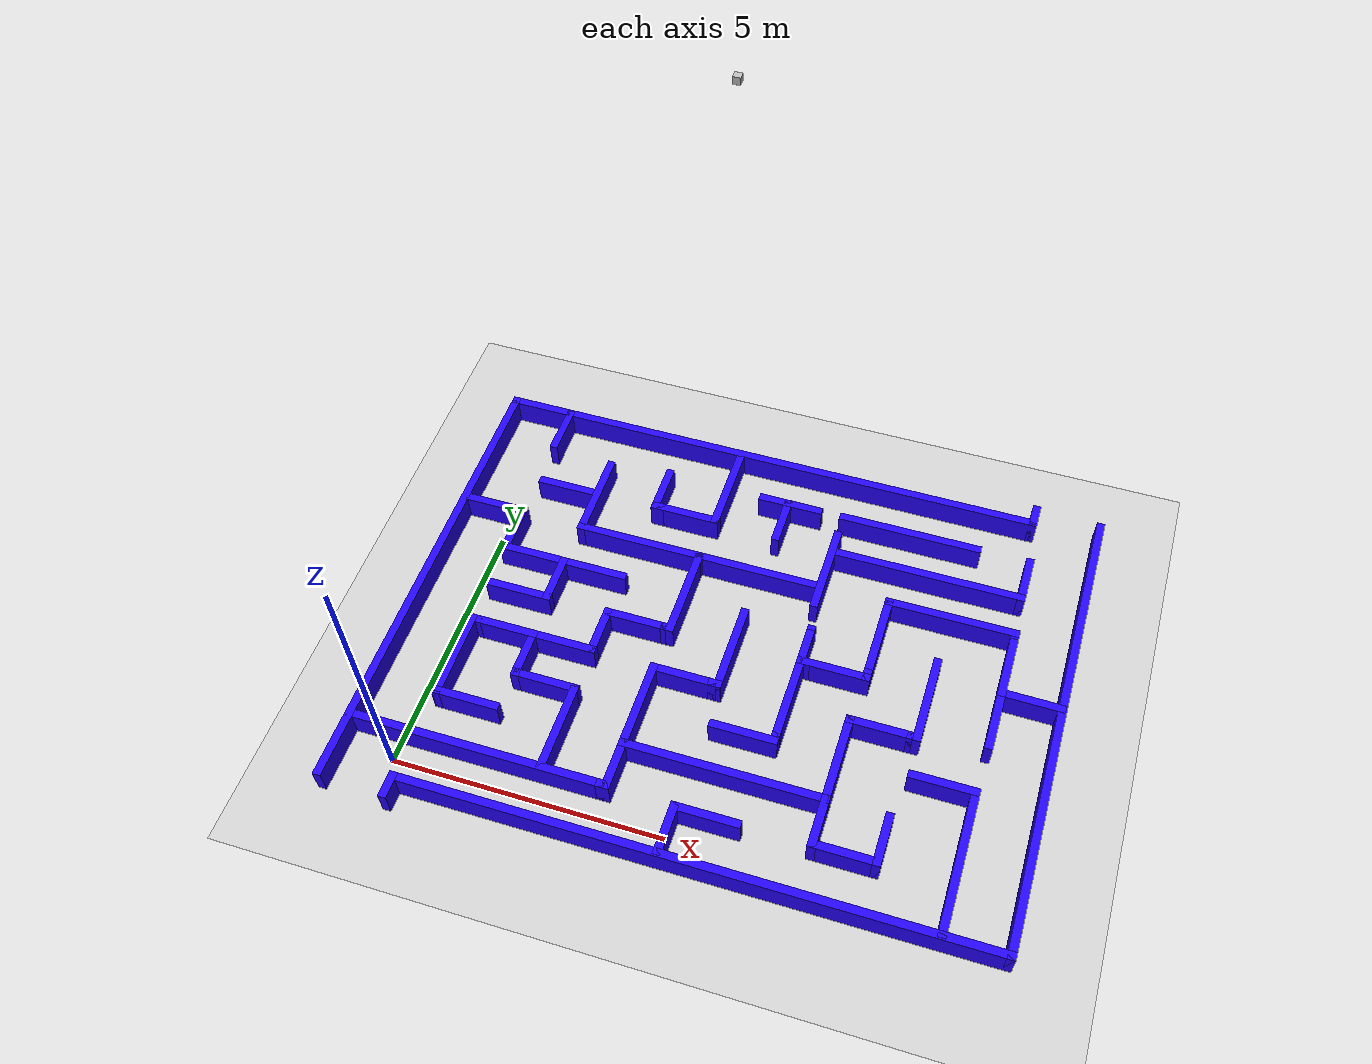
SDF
<sdf version="1.7">
 <world name="default">
  <light name="sun" type="directional">
   <pose>0 0 10 0 -0 0</pose>
   <diffuse>0.8 0.8 0.8 1</diffuse>
   <specular>0.2 0.2 0.2 1</specular>
   <attenuation>
    <range>1000</range>
    <constant>0.9</constant>
    <linear>0.01</linear>
    <quadratic>0.001</quadratic>
   </attenuation>
   <direction>-0.5 0.1 -0.9</direction>
   <spot><inner_angle>0</inner_angle><outer_angle>0</outer_angle><falloff>0</falloff></spot>
  </light>
  <model name="ground_plane">
   <static>1</static>
   <link name="link">
    <collision name="collision">
     <geometry><plane><normal>0 0 1</normal><size>100 100</size></plane></geometry>
     <surface><friction><ode><mu>100</mu><mu2>50</mu2></ode></friction></surface>
    </collision>
    <visual name="visual">
     <cast_shadows>0</cast_shadows>
     <geometry><plane><normal>0 0 1</normal><size>100 100</size></plane></geometry>
     <material>
      <script><uri>file://media/materials/scripts/gazebo.material</uri><name>Gazebo/Grey</name></script>
     </material>
    </visual>
   </link>
  </model>
  <gravity>0 0 -9.8</gravity>
  <magnetic_field>6e-06 2.3e-05 -4.2e-05</magnetic_field>
  <atmosphere type="adiabatic"/>
  <physics name="default_physics" default="0" type="ode">
   <max_step_size>0.001</max_step_size>
   <real_time_factor>1</real_time_factor>
   <real_time_update_rate>1000</real_time_update_rate>
  </physics>
  <scene><ambient>0.7 0.7 0.7 1</ambient><background>0.7 0.7 0.7 1</background><shadows>0</shadows></scene>
  <audio><device>default</device></audio>
  <spherical_coordinates>
   <surface_model>EARTH_WGS84</surface_model>
   <latitude_deg>0</latitude_deg>
   <longitude_deg>0</longitude_deg>
   <elevation>0</elevation>
   <heading_deg>0</heading_deg>
  </spherical_coordinates>
  <model name="camera_map">
   <pose>5 4 12 0 1.57 1.57</pose>
   <link name="link">
    <inertial>
     <mass>0.1</mass>
     <inertia>
      <ixx>0.000166667</ixx>
      <iyy>0.000166667</iyy>
      <izz>0.000166667</izz>
      <ixy>0</ixy>
      <ixz>0</ixz>
      <iyz>0</iyz>
     </inertia>
    </inertial>
    <collision name="collision"><geometry><box><size>0.1 0.1 0.1</size></box></geometry></collision>
    <visual name="visual"><geometry><box><size>0.1 0.1 0.1</size></box></geometry></visual>
    <sensor name="camera_map" type="camera">
     <camera>
      <horizontal_fov>1.047</horizontal_fov>
      <image><width>320</width><height>240</height></image>
      <clip><near>0.1</near><far>100</far></clip>
     </camera>
     <always_on>1</always_on>
     <update_rate>30</update_rate>
     <visualize>1</visualize>
     <plugin name="camera_controller" filename="libgazebo_ros_camera.so">
      <alwaysOn>1</alwaysOn>
      <updateRate>0.0</updateRate>
      <cameraName>camera_map</cameraName>
      <imageTopicName>image_raw</imageTopicName>
      <cameraInfoTopicName>camera_info</cameraInfoTopicName>
      <frameName>camera_link</frameName>
      <hackBaseline>0.07</hackBaseline>
      <distortionK1>0.0</distortionK1>
      <distortionK2>0.0</distortionK2>
      <distortionK3>0.0</distortionK3>
      <distortionT1>0.0</distortionT1>
      <distortionT2>0.0</distortionT2>
     </plugin>
    </sensor>
    <gravity>0</gravity>
   </link>
  </model>
  <model name="maze_blue">
   <link name="Wall_0">
    <pose>-5.9185 -0.1475 0 0 -0 1.5708</pose>
    <visual name="Wall_0_Visual">
     <pose>0 0 0.25 0 -0 0</pose>
     <geometry><box><size>9 0.15 0.5</size></box></geometry>
     <material>
      <script><uri>file://media/materials/scripts/gazebo.material</uri><name>Gazebo/Grey</name></script>
      <ambient>0.14 0.012 1 1</ambient>
      <shader type="pixel"/>
     </material>
     <meta><layer>0</layer></meta>
    </visual>
    <collision name="Wall_0_Collision">
     <pose>0 0 0.25 0 -0 0</pose>
     <geometry><box><size>9 0.15 0.5</size></box></geometry>
     <surface>
      <friction>
       <ode><mu>1</mu><mu2>1</mu2><fdir1>0 0 0</fdir1><slip1>0</slip1><slip2>0</slip2></ode>
       <torsional>
        <coefficient>1</coefficient>
        <patch_radius>0</patch_radius>
        <surface_radius>0</surface_radius>
        <use_patch_radius>1</use_patch_radius>
        <ode><slip>0</slip></ode>
       </torsional>
      </friction>
      <bounce><restitution_coefficient>0</restitution_coefficient><threshold>1e+06</threshold></bounce>
      <contact>
       <collide_without_contact>0</collide_without_contact>
       <collide_without_contact_bitmask>1</collide_without_contact_bitmask>
       <collide_bitmask>1</collide_bitmask>
       <ode>
        <soft_cfm>0</soft_cfm>
        <soft_erp>0.2</soft_erp>
        <kp>1e+13</kp>
        <kd>1</kd>
        <max_vel>0.01</max_vel>
        <min_depth>0</min_depth>
       </ode>
       <bullet>
        <split_impulse>1</split_impulse>
        <split_impulse_penetration_threshold>-0.01</split_impulse_penetration_threshold>
        <soft_cfm>0</soft_cfm>
        <soft_erp>0.2</soft_erp>
        <kp>1e+13</kp>
        <kd>1</kd>
       </bullet>
      </contact>
     </surface>
    </collision>
   </link>
   <link name="Wall_10">
    <pose>-3.5785 -3.3705 0 0 -0 0</pose>
    <visual name="Wall_10_Visual">
     <pose>0 0 0.25 0 -0 0</pose>
     <geometry><box><size>4.75 0.15 0.5</size></box></geometry>
     <material>
      <script><uri>file://media/materials/scripts/gazebo.material</uri><name>Gazebo/Grey</name></script>
      <ambient>0.14 0.012 1 1</ambient>
      <shader type="pixel"/>
     </material>
     <meta><layer>0</layer></meta>
    </visual>
    <collision name="Wall_10_Collision">
     <pose>0 0 0.25 0 -0 0</pose>
     <geometry><box><size>4.75 0.15 0.5</size></box></geometry>
     <surface>
      <friction>
       <ode><mu>1</mu><mu2>1</mu2><fdir1>0 0 0</fdir1><slip1>0</slip1><slip2>0</slip2></ode>
       <torsional>
        <coefficient>1</coefficient>
        <patch_radius>0</patch_radius>
        <surface_radius>0</surface_radius>
        <use_patch_radius>1</use_patch_radius>
        <ode><slip>0</slip></ode>
       </torsional>
      </friction>
      <bounce><restitution_coefficient>0</restitution_coefficient><threshold>1e+06</threshold></bounce>
      <contact>
       <collide_without_contact>0</collide_without_contact>
       <collide_without_contact_bitmask>1</collide_without_contact_bitmask>
       <collide_bitmask>1</collide_bitmask>
       <ode>
        <soft_cfm>0</soft_cfm>
        <soft_erp>0.2</soft_erp>
        <kp>1e+13</kp>
        <kd>1</kd>
        <max_vel>0.01</max_vel>
        <min_depth>0</min_depth>
       </ode>
       <bullet>
        <split_impulse>1</split_impulse>
        <split_impulse_penetration_threshold>-0.01</split_impulse_penetration_threshold>
        <soft_cfm>0</soft_cfm>
        <soft_erp>0.2</soft_erp>
        <kp>1e+13</kp>
        <kd>1</kd>
       </bullet>
      </contact>
     </surface>
    </collision>
   </link>
   <link name="Wall_102">
    <pose>1.2875 -1.6595 0 0 0 -1.5708</pose>
    <visual name="Wall_102_Visual">
     <pose>0 0 0.25 0 -0 0</pose>
     <geometry><box><size>0.25 0.15 0.5</size></box></geometry>
     <material>
      <script><uri>file://media/materials/scripts/gazebo.material</uri><name>Gazebo/Grey</name></script>
      <ambient>0.14 0.012 1 1</ambient>
      <shader type="pixel"/>
     </material>
     <meta><layer>0</layer></meta>
    </visual>
    <collision name="Wall_102_Collision">
     <pose>0 0 0.25 0 -0 0</pose>
     <geometry><box><size>0.25 0.15 0.5</size></box></geometry>
     <surface>
      <friction>
       <ode><mu>1</mu><mu2>1</mu2><fdir1>0 0 0</fdir1><slip1>0</slip1><slip2>0</slip2></ode>
       <torsional>
        <coefficient>1</coefficient>
        <patch_radius>0</patch_radius>
        <surface_radius>0</surface_radius>
        <use_patch_radius>1</use_patch_radius>
        <ode><slip>0</slip></ode>
       </torsional>
      </friction>
      <bounce><restitution_coefficient>0</restitution_coefficient><threshold>1e+06</threshold></bounce>
      <contact>
       <collide_without_contact>0</collide_without_contact>
       <collide_without_contact_bitmask>1</collide_without_contact_bitmask>
       <collide_bitmask>1</collide_bitmask>
       <ode>
        <soft_cfm>0</soft_cfm>
        <soft_erp>0.2</soft_erp>
        <kp>1e+13</kp>
        <kd>1</kd>
        <max_vel>0.01</max_vel>
        <min_depth>0</min_depth>
       </ode>
       <bullet>
        <split_impulse>1</split_impulse>
        <split_impulse_penetration_threshold>-0.01</split_impulse_penetration_threshold>
        <soft_cfm>0</soft_cfm>
        <soft_erp>0.2</soft_erp>
        <kp>1e+13</kp>
        <kd>1</kd>
       </bullet>
      </contact>
     </surface>
    </collision>
   </link>
   <link name="Wall_103">
    <pose>0.7375 -1.7095 0 0 -0 3.14159</pose>
    <visual name="Wall_103_Visual">
     <pose>0 0 0.25 0 -0 0</pose>
     <geometry><box><size>1.25 0.15 0.5</size></box></geometry>
     <material>
      <script><uri>file://media/materials/scripts/gazebo.material</uri><name>Gazebo/Grey</name></script>
      <ambient>0.14 0.012 1 1</ambient>
      <shader type="pixel"/>
     </material>
     <meta><layer>0</layer></meta>
    </visual>
    <collision name="Wall_103_Collision">
     <pose>0 0 0.25 0 -0 0</pose>
     <geometry><box><size>1.25 0.15 0.5</size></box></geometry>
     <surface>
      <friction>
       <ode><mu>1</mu><mu2>1</mu2><fdir1>0 0 0</fdir1><slip1>0</slip1><slip2>0</slip2></ode>
       <torsional>
        <coefficient>1</coefficient>
        <patch_radius>0</patch_radius>
        <surface_radius>0</surface_radius>
        <use_patch_radius>1</use_patch_radius>
        <ode><slip>0</slip></ode>
       </torsional>
      </friction>
      <bounce><restitution_coefficient>0</restitution_coefficient><threshold>1e+06</threshold></bounce>
      <contact>
       <collide_without_contact>0</collide_without_contact>
       <collide_without_contact_bitmask>1</collide_without_contact_bitmask>
       <collide_bitmask>1</collide_bitmask>
       <ode>
        <soft_cfm>0</soft_cfm>
        <soft_erp>0.2</soft_erp>
        <kp>1e+13</kp>
        <kd>1</kd>
        <max_vel>0.01</max_vel>
        <min_depth>0</min_depth>
       </ode>
       <bullet>
        <split_impulse>1</split_impulse>
        <split_impulse_penetration_threshold>-0.01</split_impulse_penetration_threshold>
        <soft_cfm>0</soft_cfm>
        <soft_erp>0.2</soft_erp>
        <kp>1e+13</kp>
        <kd>1</kd>
       </bullet>
      </contact>
     </surface>
    </collision>
   </link>
   <link name="Wall_13">
    <pose>-1.2285 -3.3705 0 0 -0 0</pose>
    <visual name="Wall_13_Visual">
     <pose>0 0 0.25 0 -0 0</pose>
     <geometry><box><size>0.25 0.15 0.5</size></box></geometry>
     <material>
      <script><uri>file://media/materials/scripts/gazebo.material</uri><name>Gazebo/Grey</name></script>
      <ambient>0.14 0.012 1 1</ambient>
      <shader type="pixel"/>
     </material>
     <meta><layer>0</layer></meta>
    </visual>
    <collision name="Wall_13_Collision">
     <pose>0 0 0.25 0 -0 0</pose>
     <geometry><box><size>0.25 0.15 0.5</size></box></geometry>
     <surface>
      <friction>
       <ode><mu>1</mu><mu2>1</mu2><fdir1>0 0 0</fdir1><slip1>0</slip1><slip2>0</slip2></ode>
       <torsional>
        <coefficient>1</coefficient>
        <patch_radius>0</patch_radius>
        <surface_radius>0</surface_radius>
        <use_patch_radius>1</use_patch_radius>
        <ode><slip>0</slip></ode>
       </torsional>
      </friction>
      <bounce><restitution_coefficient>0</restitution_coefficient><threshold>1e+06</threshold></bounce>
      <contact>
       <collide_without_contact>0</collide_without_contact>
       <collide_without_contact_bitmask>1</collide_without_contact_bitmask>
       <collide_bitmask>1</collide_bitmask>
       <ode>
        <soft_cfm>0</soft_cfm>
        <soft_erp>0.2</soft_erp>
        <kp>1e+13</kp>
        <kd>1</kd>
        <max_vel>0.01</max_vel>
        <min_depth>0</min_depth>
       </ode>
       <bullet>
        <split_impulse>1</split_impulse>
        <split_impulse_penetration_threshold>-0.01</split_impulse_penetration_threshold>
        <soft_cfm>0</soft_cfm>
        <soft_erp>0.2</soft_erp>
        <kp>1e+13</kp>
        <kd>1</kd>
       </bullet>
      </contact>
     </surface>
    </collision>
   </link>
   <link name="Wall_14">
    <pose>-1.1785 -2.9455 0 0 -0 1.5708</pose>
    <visual name="Wall_14_Visual">
     <pose>0 0 0.25 0 -0 0</pose>
     <geometry><box><size>1 0.15 0.5</size></box></geometry>
     <material>
      <script><uri>file://media/materials/scripts/gazebo.material</uri><name>Gazebo/Grey</name></script>
      <ambient>0.14 0.012 1 1</ambient>
      <shader type="pixel"/>
     </material>
     <meta><layer>0</layer></meta>
    </visual>
    <collision name="Wall_14_Collision">
     <pose>0 0 0.25 0 -0 0</pose>
     <geometry><box><size>1 0.15 0.5</size></box></geometry>
     <surface>
      <friction>
       <ode><mu>1</mu><mu2>1</mu2><fdir1>0 0 0</fdir1><slip1>0</slip1><slip2>0</slip2></ode>
       <torsional>
        <coefficient>1</coefficient>
        <patch_radius>0</patch_radius>
        <surface_radius>0</surface_radius>
        <use_patch_radius>1</use_patch_radius>
        <ode><slip>0</slip></ode>
       </torsional>
      </friction>
      <bounce><restitution_coefficient>0</restitution_coefficient><threshold>1e+06</threshold></bounce>
      <contact>
       <collide_without_contact>0</collide_without_contact>
       <collide_without_contact_bitmask>1</collide_without_contact_bitmask>
       <collide_bitmask>1</collide_bitmask>
       <ode>
        <soft_cfm>0</soft_cfm>
        <soft_erp>0.2</soft_erp>
        <kp>1e+13</kp>
        <kd>1</kd>
        <max_vel>0.01</max_vel>
        <min_depth>0</min_depth>
       </ode>
       <bullet>
        <split_impulse>1</split_impulse>
        <split_impulse_penetration_threshold>-0.01</split_impulse_penetration_threshold>
        <soft_cfm>0</soft_cfm>
        <soft_erp>0.2</soft_erp>
        <kp>1e+13</kp>
        <kd>1</kd>
       </bullet>
      </contact>
     </surface>
    </collision>
   </link>
   <link name="Wall_15">
    <pose>0.6215 -2.5205 0 0 -0 0</pose>
    <visual name="Wall_15_Visual">
     <pose>0 0 0.25 0 -0 0</pose>
     <geometry><box><size>3.75 0.15 0.5</size></box></geometry>
     <material>
      <script><uri>file://media/materials/scripts/gazebo.material</uri><name>Gazebo/Grey</name></script>
      <ambient>0.14 0.012 1 1</ambient>
      <shader type="pixel"/>
     </material>
     <meta><layer>0</layer></meta>
    </visual>
    <collision name="Wall_15_Collision">
     <pose>0 0 0.25 0 -0 0</pose>
     <geometry><box><size>3.75 0.15 0.5</size></box></geometry>
     <surface>
      <friction>
       <ode><mu>1</mu><mu2>1</mu2><fdir1>0 0 0</fdir1><slip1>0</slip1><slip2>0</slip2></ode>
       <torsional>
        <coefficient>1</coefficient>
        <patch_radius>0</patch_radius>
        <surface_radius>0</surface_radius>
        <use_patch_radius>1</use_patch_radius>
        <ode><slip>0</slip></ode>
       </torsional>
      </friction>
      <bounce><restitution_coefficient>0</restitution_coefficient><threshold>1e+06</threshold></bounce>
      <contact>
       <collide_without_contact>0</collide_without_contact>
       <collide_without_contact_bitmask>1</collide_without_contact_bitmask>
       <collide_bitmask>1</collide_bitmask>
       <ode>
        <soft_cfm>0</soft_cfm>
        <soft_erp>0.2</soft_erp>
        <kp>1e+13</kp>
        <kd>1</kd>
        <max_vel>0.01</max_vel>
        <min_depth>0</min_depth>
       </ode>
       <bullet>
        <split_impulse>1</split_impulse>
        <split_impulse_penetration_threshold>-0.01</split_impulse_penetration_threshold>
        <soft_cfm>0</soft_cfm>
        <soft_erp>0.2</soft_erp>
        <kp>1e+13</kp>
        <kd>1</kd>
       </bullet>
      </contact>
     </surface>
    </collision>
   </link>
   <link name="Wall_16">
    <pose>2.4215 -2.9455 0 0 0 -1.5708</pose>
    <visual name="Wall_16_Visual">
     <pose>0 0 0.25 0 -0 0</pose>
     <geometry><box><size>1 0.15 0.5</size></box></geometry>
     <material>
      <script><uri>file://media/materials/scripts/gazebo.material</uri><name>Gazebo/Grey</name></script>
      <ambient>0.14 0.012 1 1</ambient>
      <shader type="pixel"/>
     </material>
     <meta><layer>0</layer></meta>
    </visual>
    <collision name="Wall_16_Collision">
     <pose>0 0 0.25 0 -0 0</pose>
     <geometry><box><size>1 0.15 0.5</size></box></geometry>
     <surface>
      <friction>
       <ode><mu>1</mu><mu2>1</mu2><fdir1>0 0 0</fdir1><slip1>0</slip1><slip2>0</slip2></ode>
       <torsional>
        <coefficient>1</coefficient>
        <patch_radius>0</patch_radius>
        <surface_radius>0</surface_radius>
        <use_patch_radius>1</use_patch_radius>
        <ode><slip>0</slip></ode>
       </torsional>
      </friction>
      <bounce><restitution_coefficient>0</restitution_coefficient><threshold>1e+06</threshold></bounce>
      <contact>
       <collide_without_contact>0</collide_without_contact>
       <collide_without_contact_bitmask>1</collide_without_contact_bitmask>
       <collide_bitmask>1</collide_bitmask>
       <ode>
        <soft_cfm>0</soft_cfm>
        <soft_erp>0.2</soft_erp>
        <kp>1e+13</kp>
        <kd>1</kd>
        <max_vel>0.01</max_vel>
        <min_depth>0</min_depth>
       </ode>
       <bullet>
        <split_impulse>1</split_impulse>
        <split_impulse_penetration_threshold>-0.01</split_impulse_penetration_threshold>
        <soft_cfm>0</soft_cfm>
        <soft_erp>0.2</soft_erp>
        <kp>1e+13</kp>
        <kd>1</kd>
       </bullet>
      </contact>
     </surface>
    </collision>
   </link>
   <link name="Wall_17">
    <pose>2.9715 -3.3705 0 0 -0 0</pose>
    <visual name="Wall_17_Visual">
     <pose>0 0 0.25 0 -0 0</pose>
     <geometry><box><size>1.25 0.15 0.5</size></box></geometry>
     <material>
      <script><uri>file://media/materials/scripts/gazebo.material</uri><name>Gazebo/Grey</name></script>
      <ambient>0.14 0.012 1 1</ambient>
      <shader type="pixel"/>
     </material>
     <meta><layer>0</layer></meta>
    </visual>
    <collision name="Wall_17_Collision">
     <pose>0 0 0.25 0 -0 0</pose>
     <geometry><box><size>1.25 0.15 0.5</size></box></geometry>
     <surface>
      <friction>
       <ode><mu>1</mu><mu2>1</mu2><fdir1>0 0 0</fdir1><slip1>0</slip1><slip2>0</slip2></ode>
       <torsional>
        <coefficient>1</coefficient>
        <patch_radius>0</patch_radius>
        <surface_radius>0</surface_radius>
        <use_patch_radius>1</use_patch_radius>
        <ode><slip>0</slip></ode>
       </torsional>
      </friction>
      <bounce><restitution_coefficient>0</restitution_coefficient><threshold>1e+06</threshold></bounce>
      <contact>
       <collide_without_contact>0</collide_without_contact>
       <collide_without_contact_bitmask>1</collide_without_contact_bitmask>
       <collide_bitmask>1</collide_bitmask>
       <ode>
        <soft_cfm>0</soft_cfm>
        <soft_erp>0.2</soft_erp>
        <kp>1e+13</kp>
        <kd>1</kd>
        <max_vel>0.01</max_vel>
        <min_depth>0</min_depth>
       </ode>
       <bullet>
        <split_impulse>1</split_impulse>
        <split_impulse_penetration_threshold>-0.01</split_impulse_penetration_threshold>
        <soft_cfm>0</soft_cfm>
        <soft_erp>0.2</soft_erp>
        <kp>1e+13</kp>
        <kd>1</kd>
       </bullet>
      </contact>
     </surface>
    </collision>
   </link>
   <link name="Wall_18">
    <pose>3.5215 -2.9455 0 0 -0 1.5708</pose>
    <visual name="Wall_18_Visual">
     <pose>0 0 0.25 0 -0 0</pose>
     <geometry><box><size>1 0.15 0.5</size></box></geometry>
     <material>
      <script><uri>file://media/materials/scripts/gazebo.material</uri><name>Gazebo/Grey</name></script>
      <ambient>0.14 0.012 1 1</ambient>
      <shader type="pixel"/>
     </material>
     <meta><layer>0</layer></meta>
    </visual>
    <collision name="Wall_18_Collision">
     <pose>0 0 0.25 0 -0 0</pose>
     <geometry><box><size>1 0.15 0.5</size></box></geometry>
     <surface>
      <friction>
       <ode><mu>1</mu><mu2>1</mu2><fdir1>0 0 0</fdir1><slip1>0</slip1><slip2>0</slip2></ode>
       <torsional>
        <coefficient>1</coefficient>
        <patch_radius>0</patch_radius>
        <surface_radius>0</surface_radius>
        <use_patch_radius>1</use_patch_radius>
        <ode><slip>0</slip></ode>
       </torsional>
      </friction>
      <bounce><restitution_coefficient>0</restitution_coefficient><threshold>1e+06</threshold></bounce>
      <contact>
       <collide_without_contact>0</collide_without_contact>
       <collide_without_contact_bitmask>1</collide_without_contact_bitmask>
       <collide_bitmask>1</collide_bitmask>
       <ode>
        <soft_cfm>0</soft_cfm>
        <soft_erp>0.2</soft_erp>
        <kp>1e+13</kp>
        <kd>1</kd>
        <max_vel>0.01</max_vel>
        <min_depth>0</min_depth>
       </ode>
       <bullet>
        <split_impulse>1</split_impulse>
        <split_impulse_penetration_threshold>-0.01</split_impulse_penetration_threshold>
        <soft_cfm>0</soft_cfm>
        <soft_erp>0.2</soft_erp>
        <kp>1e+13</kp>
        <kd>1</kd>
       </bullet>
      </contact>
     </surface>
    </collision>
   </link>
   <link name="Wall_2">
    <pose>-0.6185 4.2775 0 0 -0 0</pose>
    <visual name="Wall_2_Visual">
     <pose>0 0 0.25 0 -0 0</pose>
     <geometry><box><size>10.75 0.15 0.5</size></box></geometry>
     <material>
      <script><uri>file://media/materials/scripts/gazebo.material</uri><name>Gazebo/Grey</name></script>
      <ambient>0.14 0.012 1 1</ambient>
      <shader type="pixel"/>
     </material>
     <meta><layer>0</layer></meta>
    </visual>
    <collision name="Wall_2_Collision">
     <pose>0 0 0.25 0 -0 0</pose>
     <geometry><box><size>10.75 0.15 0.5</size></box></geometry>
     <surface>
      <friction>
       <ode><mu>1</mu><mu2>1</mu2><fdir1>0 0 0</fdir1><slip1>0</slip1><slip2>0</slip2></ode>
       <torsional>
        <coefficient>1</coefficient>
        <patch_radius>0</patch_radius>
        <surface_radius>0</surface_radius>
        <use_patch_radius>1</use_patch_radius>
        <ode><slip>0</slip></ode>
       </torsional>
      </friction>
      <bounce><restitution_coefficient>0</restitution_coefficient><threshold>1e+06</threshold></bounce>
      <contact>
       <collide_without_contact>0</collide_without_contact>
       <collide_without_contact_bitmask>1</collide_without_contact_bitmask>
       <collide_bitmask>1</collide_bitmask>
       <ode>
        <soft_cfm>0</soft_cfm>
        <soft_erp>0.2</soft_erp>
        <kp>1e+13</kp>
        <kd>1</kd>
        <max_vel>0.01</max_vel>
        <min_depth>0</min_depth>
       </ode>
       <bullet>
        <split_impulse>1</split_impulse>
        <split_impulse_penetration_threshold>-0.01</split_impulse_penetration_threshold>
        <soft_cfm>0</soft_cfm>
        <soft_erp>0.2</soft_erp>
        <kp>1e+13</kp>
        <kd>1</kd>
       </bullet>
      </contact>
     </surface>
    </collision>
   </link>
   <link name="Wall_20">
    <pose>0.0445 -3.8205 0 0 -0 1.5708</pose>
    <visual name="Wall_20_Visual">
     <pose>0 0 0.25 0 -0 0</pose>
     <geometry><box><size>1 0.15 0.5</size></box></geometry>
     <material>
      <script><uri>file://media/materials/scripts/gazebo.material</uri><name>Gazebo/Grey</name></script>
      <ambient>0.14 0.012 1 1</ambient>
      <shader type="pixel"/>
     </material>
     <meta><layer>0</layer></meta>
    </visual>
    <collision name="Wall_20_Collision">
     <pose>0 0 0.25 0 -0 0</pose>
     <geometry><box><size>1 0.15 0.5</size></box></geometry>
     <surface>
      <friction>
       <ode><mu>1</mu><mu2>1</mu2><fdir1>0 0 0</fdir1><slip1>0</slip1><slip2>0</slip2></ode>
       <torsional>
        <coefficient>1</coefficient>
        <patch_radius>0</patch_radius>
        <surface_radius>0</surface_radius>
        <use_patch_radius>1</use_patch_radius>
        <ode><slip>0</slip></ode>
       </torsional>
      </friction>
      <bounce><restitution_coefficient>0</restitution_coefficient><threshold>1e+06</threshold></bounce>
      <contact>
       <collide_without_contact>0</collide_without_contact>
       <collide_without_contact_bitmask>1</collide_without_contact_bitmask>
       <collide_bitmask>1</collide_bitmask>
       <ode>
        <soft_cfm>0</soft_cfm>
        <soft_erp>0.2</soft_erp>
        <kp>1e+13</kp>
        <kd>1</kd>
        <max_vel>0.01</max_vel>
        <min_depth>0</min_depth>
       </ode>
       <bullet>
        <split_impulse>1</split_impulse>
        <split_impulse_penetration_threshold>-0.01</split_impulse_penetration_threshold>
        <soft_cfm>0</soft_cfm>
        <soft_erp>0.2</soft_erp>
        <kp>1e+13</kp>
        <kd>1</kd>
       </bullet>
      </contact>
     </surface>
    </collision>
   </link>
   <link name="Wall_21">
    <pose>0.5945 -3.3955 0 0 -0 0</pose>
    <visual name="Wall_21_Visual">
     <pose>0 0 0.25 0 -0 0</pose>
     <geometry><box><size>1.25 0.15 0.5</size></box></geometry>
     <material>
      <script><uri>file://media/materials/scripts/gazebo.material</uri><name>Gazebo/Grey</name></script>
      <ambient>0.14 0.012 1 1</ambient>
      <shader type="pixel"/>
     </material>
     <meta><layer>0</layer></meta>
    </visual>
    <collision name="Wall_21_Collision">
     <pose>0 0 0.25 0 -0 0</pose>
     <geometry><box><size>1.25 0.15 0.5</size></box></geometry>
     <surface>
      <friction>
       <ode><mu>1</mu><mu2>1</mu2><fdir1>0 0 0</fdir1><slip1>0</slip1><slip2>0</slip2></ode>
       <torsional>
        <coefficient>1</coefficient>
        <patch_radius>0</patch_radius>
        <surface_radius>0</surface_radius>
        <use_patch_radius>1</use_patch_radius>
        <ode><slip>0</slip></ode>
       </torsional>
      </friction>
      <bounce><restitution_coefficient>0</restitution_coefficient><threshold>1e+06</threshold></bounce>
      <contact>
       <collide_without_contact>0</collide_without_contact>
       <collide_without_contact_bitmask>1</collide_without_contact_bitmask>
       <collide_bitmask>1</collide_bitmask>
       <ode>
        <soft_cfm>0</soft_cfm>
        <soft_erp>0.2</soft_erp>
        <kp>1e+13</kp>
        <kd>1</kd>
        <max_vel>0.01</max_vel>
        <min_depth>0</min_depth>
       </ode>
       <bullet>
        <split_impulse>1</split_impulse>
        <split_impulse_penetration_threshold>-0.01</split_impulse_penetration_threshold>
        <soft_cfm>0</soft_cfm>
        <soft_erp>0.2</soft_erp>
        <kp>1e+13</kp>
        <kd>1</kd>
       </bullet>
      </contact>
     </surface>
    </collision>
   </link>
   <link name="Wall_23">
    <pose>4.8015 -2.9455 0 0 -0 1.5708</pose>
    <visual name="Wall_23_Visual">
     <pose>0 0 0.25 0 -0 0</pose>
     <geometry><box><size>2.75 0.15 0.5</size></box></geometry>
     <material>
      <script><uri>file://media/materials/scripts/gazebo.material</uri><name>Gazebo/Grey</name></script>
      <ambient>0.14 0.012 1 1</ambient>
      <shader type="pixel"/>
     </material>
     <meta><layer>0</layer></meta>
    </visual>
    <collision name="Wall_23_Collision">
     <pose>0 0 0.25 0 -0 0</pose>
     <geometry><box><size>2.75 0.15 0.5</size></box></geometry>
     <surface>
      <friction>
       <ode><mu>1</mu><mu2>1</mu2><fdir1>0 0 0</fdir1><slip1>0</slip1><slip2>0</slip2></ode>
       <torsional>
        <coefficient>1</coefficient>
        <patch_radius>0</patch_radius>
        <surface_radius>0</surface_radius>
        <use_patch_radius>1</use_patch_radius>
        <ode><slip>0</slip></ode>
       </torsional>
      </friction>
      <bounce><restitution_coefficient>0</restitution_coefficient><threshold>1e+06</threshold></bounce>
      <contact>
       <collide_without_contact>0</collide_without_contact>
       <collide_without_contact_bitmask>1</collide_without_contact_bitmask>
       <collide_bitmask>1</collide_bitmask>
       <ode>
        <soft_cfm>0</soft_cfm>
        <soft_erp>0.2</soft_erp>
        <kp>1e+13</kp>
        <kd>1</kd>
        <max_vel>0.01</max_vel>
        <min_depth>0</min_depth>
       </ode>
       <bullet>
        <split_impulse>1</split_impulse>
        <split_impulse_penetration_threshold>-0.01</split_impulse_penetration_threshold>
        <soft_cfm>0</soft_cfm>
        <soft_erp>0.2</soft_erp>
        <kp>1e+13</kp>
        <kd>1</kd>
       </bullet>
      </contact>
     </surface>
    </collision>
   </link>
   <link name="Wall_24">
    <pose>4.2515 -1.6455 0 0 -0 3.14159</pose>
    <visual name="Wall_24_Visual">
     <pose>0 0 0.25 0 -0 0</pose>
     <geometry><box><size>1.25 0.15 0.5</size></box></geometry>
     <material>
      <script><uri>file://media/materials/scripts/gazebo.material</uri><name>Gazebo/Grey</name></script>
      <ambient>0.14 0.012 1 1</ambient>
      <shader type="pixel"/>
     </material>
     <meta><layer>0</layer></meta>
    </visual>
    <collision name="Wall_24_Collision">
     <pose>0 0 0.25 0 -0 0</pose>
     <geometry><box><size>1.25 0.15 0.5</size></box></geometry>
     <surface>
      <friction>
       <ode><mu>1</mu><mu2>1</mu2><fdir1>0 0 0</fdir1><slip1>0</slip1><slip2>0</slip2></ode>
       <torsional>
        <coefficient>1</coefficient>
        <patch_radius>0</patch_radius>
        <surface_radius>0</surface_radius>
        <use_patch_radius>1</use_patch_radius>
        <ode><slip>0</slip></ode>
       </torsional>
      </friction>
      <bounce><restitution_coefficient>0</restitution_coefficient><threshold>1e+06</threshold></bounce>
      <contact>
       <collide_without_contact>0</collide_without_contact>
       <collide_without_contact_bitmask>1</collide_without_contact_bitmask>
       <collide_bitmask>1</collide_bitmask>
       <ode>
        <soft_cfm>0</soft_cfm>
        <soft_erp>0.2</soft_erp>
        <kp>1e+13</kp>
        <kd>1</kd>
        <max_vel>0.01</max_vel>
        <min_depth>0</min_depth>
       </ode>
       <bullet>
        <split_impulse>1</split_impulse>
        <split_impulse_penetration_threshold>-0.01</split_impulse_penetration_threshold>
        <soft_cfm>0</soft_cfm>
        <soft_erp>0.2</soft_erp>
        <kp>1e+13</kp>
        <kd>1</kd>
       </bullet>
      </contact>
     </surface>
    </collision>
   </link>
   <link name="Wall_26">
    <pose>-2.3595 -2.5505 0 0 -0 1.5708</pose>
    <visual name="Wall_26_Visual">
     <pose>0 0 0.25 0 -0 0</pose>
     <geometry><box><size>1.75 0.15 0.5</size></box></geometry>
     <material>
      <script><uri>file://media/materials/scripts/gazebo.material</uri><name>Gazebo/Grey</name></script>
      <ambient>0.14 0.012 1 1</ambient>
      <shader type="pixel"/>
     </material>
     <meta><layer>0</layer></meta>
    </visual>
    <collision name="Wall_26_Collision">
     <pose>0 0 0.25 0 -0 0</pose>
     <geometry><box><size>1.75 0.15 0.5</size></box></geometry>
     <surface>
      <friction>
       <ode><mu>1</mu><mu2>1</mu2><fdir1>0 0 0</fdir1><slip1>0</slip1><slip2>0</slip2></ode>
       <torsional>
        <coefficient>1</coefficient>
        <patch_radius>0</patch_radius>
        <surface_radius>0</surface_radius>
        <use_patch_radius>1</use_patch_radius>
        <ode><slip>0</slip></ode>
       </torsional>
      </friction>
      <bounce><restitution_coefficient>0</restitution_coefficient><threshold>1e+06</threshold></bounce>
      <contact>
       <collide_without_contact>0</collide_without_contact>
       <collide_without_contact_bitmask>1</collide_without_contact_bitmask>
       <collide_bitmask>1</collide_bitmask>
       <ode>
        <soft_cfm>0</soft_cfm>
        <soft_erp>0.2</soft_erp>
        <kp>1e+13</kp>
        <kd>1</kd>
        <max_vel>0.01</max_vel>
        <min_depth>0</min_depth>
       </ode>
       <bullet>
        <split_impulse>1</split_impulse>
        <split_impulse_penetration_threshold>-0.01</split_impulse_penetration_threshold>
        <soft_cfm>0</soft_cfm>
        <soft_erp>0.2</soft_erp>
        <kp>1e+13</kp>
        <kd>1</kd>
       </bullet>
      </contact>
     </surface>
    </collision>
   </link>
   <link name="Wall_27">
    <pose>-2.918 -1.7505 0 0 -0 3.14159</pose>
    <visual name="Wall_27_Visual">
     <pose>0 0 0.25 0 -0 0</pose>
     <geometry><box><size>1.26736 0.15 0.5</size></box></geometry>
     <material>
      <script><uri>file://media/materials/scripts/gazebo.material</uri><name>Gazebo/Grey</name></script>
      <ambient>0.14 0.012 1 1</ambient>
      <shader type="pixel"/>
     </material>
     <meta><layer>0</layer></meta>
    </visual>
    <collision name="Wall_27_Collision">
     <pose>0 0 0.25 0 -0 0</pose>
     <geometry><box><size>1.26736 0.15 0.5</size></box></geometry>
     <surface>
      <friction>
       <ode><mu>1</mu><mu2>1</mu2><fdir1>0 0 0</fdir1><slip1>0</slip1><slip2>0</slip2></ode>
       <torsional>
        <coefficient>1</coefficient>
        <patch_radius>0</patch_radius>
        <surface_radius>0</surface_radius>
        <use_patch_radius>1</use_patch_radius>
        <ode><slip>0</slip></ode>
       </torsional>
      </friction>
      <bounce><restitution_coefficient>0</restitution_coefficient><threshold>1e+06</threshold></bounce>
      <contact>
       <collide_without_contact>0</collide_without_contact>
       <collide_without_contact_bitmask>1</collide_without_contact_bitmask>
       <collide_bitmask>1</collide_bitmask>
       <ode>
        <soft_cfm>0</soft_cfm>
        <soft_erp>0.2</soft_erp>
        <kp>1e+13</kp>
        <kd>1</kd>
        <max_vel>0.01</max_vel>
        <min_depth>0</min_depth>
       </ode>
       <bullet>
        <split_impulse>1</split_impulse>
        <split_impulse_penetration_threshold>-0.01</split_impulse_penetration_threshold>
        <soft_cfm>0</soft_cfm>
        <soft_erp>0.2</soft_erp>
        <kp>1e+13</kp>
        <kd>1</kd>
       </bullet>
      </contact>
     </surface>
    </collision>
   </link>
   <link name="Wall_28">
    <pose>-3.4765 -1.3255 0 0 -0 1.5708</pose>
    <visual name="Wall_28_Visual">
     <pose>0 0 0.25 0 -0 0</pose>
     <geometry><box><size>1.00034 0.15 0.5</size></box></geometry>
     <material>
      <script><uri>file://media/materials/scripts/gazebo.material</uri><name>Gazebo/Grey</name></script>
      <ambient>0.14 0.012 1 1</ambient>
      <shader type="pixel"/>
     </material>
     <meta><layer>0</layer></meta>
    </visual>
    <collision name="Wall_28_Collision">
     <pose>0 0 0.25 0 -0 0</pose>
     <geometry><box><size>1.00034 0.15 0.5</size></box></geometry>
     <surface>
      <friction>
       <ode><mu>1</mu><mu2>1</mu2><fdir1>0 0 0</fdir1><slip1>0</slip1><slip2>0</slip2></ode>
       <torsional>
        <coefficient>1</coefficient>
        <patch_radius>0</patch_radius>
        <surface_radius>0</surface_radius>
        <use_patch_radius>1</use_patch_radius>
        <ode><slip>0</slip></ode>
       </torsional>
      </friction>
      <bounce><restitution_coefficient>0</restitution_coefficient><threshold>1e+06</threshold></bounce>
      <contact>
       <collide_without_contact>0</collide_without_contact>
       <collide_without_contact_bitmask>1</collide_without_contact_bitmask>
       <collide_bitmask>1</collide_bitmask>
       <ode>
        <soft_cfm>0</soft_cfm>
        <soft_erp>0.2</soft_erp>
        <kp>1e+13</kp>
        <kd>1</kd>
        <max_vel>0.01</max_vel>
        <min_depth>0</min_depth>
       </ode>
       <bullet>
        <split_impulse>1</split_impulse>
        <split_impulse_penetration_threshold>-0.01</split_impulse_penetration_threshold>
        <soft_cfm>0</soft_cfm>
        <soft_erp>0.2</soft_erp>
        <kp>1e+13</kp>
        <kd>1</kd>
       </bullet>
      </contact>
     </surface>
    </collision>
   </link>
   <link name="Wall_29">
    <pose>-4.018 -0.9005 0 0 -0 3.14159</pose>
    <visual name="Wall_29_Visual">
     <pose>0 0 0.25 0 -0 0</pose>
     <geometry><box><size>1.23267 0.15 0.5</size></box></geometry>
     <material>
      <script><uri>file://media/materials/scripts/gazebo.material</uri><name>Gazebo/Grey</name></script>
      <ambient>0.14 0.012 1 1</ambient>
      <shader type="pixel"/>
     </material>
     <meta><layer>0</layer></meta>
    </visual>
    <collision name="Wall_29_Collision">
     <pose>0 0 0.25 0 -0 0</pose>
     <geometry><box><size>1.23267 0.15 0.5</size></box></geometry>
     <surface>
      <friction>
       <ode><mu>1</mu><mu2>1</mu2><fdir1>0 0 0</fdir1><slip1>0</slip1><slip2>0</slip2></ode>
       <torsional>
        <coefficient>1</coefficient>
        <patch_radius>0</patch_radius>
        <surface_radius>0</surface_radius>
        <use_patch_radius>1</use_patch_radius>
        <ode><slip>0</slip></ode>
       </torsional>
      </friction>
      <bounce><restitution_coefficient>0</restitution_coefficient><threshold>1e+06</threshold></bounce>
      <contact>
       <collide_without_contact>0</collide_without_contact>
       <collide_without_contact_bitmask>1</collide_without_contact_bitmask>
       <collide_bitmask>1</collide_bitmask>
       <ode>
        <soft_cfm>0</soft_cfm>
        <soft_erp>0.2</soft_erp>
        <kp>1e+13</kp>
        <kd>1</kd>
        <max_vel>0.01</max_vel>
        <min_depth>0</min_depth>
       </ode>
       <bullet>
        <split_impulse>1</split_impulse>
        <split_impulse_penetration_threshold>-0.01</split_impulse_penetration_threshold>
        <soft_cfm>0</soft_cfm>
        <soft_erp>0.2</soft_erp>
        <kp>1e+13</kp>
        <kd>1</kd>
       </bullet>
      </contact>
     </surface>
    </collision>
   </link>
   <link name="Wall_3">
    <pose>4.6815 4.4525 0 0 -0 1.5708</pose>
    <visual name="Wall_3_Visual">
     <pose>0 0 0.25 0 -0 0</pose>
     <geometry><box><size>0.5 0.15 0.5</size></box></geometry>
     <material>
      <script><uri>file://media/materials/scripts/gazebo.material</uri><name>Gazebo/Grey</name></script>
      <ambient>0.14 0.012 1 1</ambient>
      <shader type="pixel"/>
     </material>
     <meta><layer>0</layer></meta>
    </visual>
    <collision name="Wall_3_Collision">
     <pose>0 0 0.25 0 -0 0</pose>
     <geometry><box><size>0.5 0.15 0.5</size></box></geometry>
     <surface>
      <friction>
       <ode><mu>1</mu><mu2>1</mu2><fdir1>0 0 0</fdir1><slip1>0</slip1><slip2>0</slip2></ode>
       <torsional>
        <coefficient>1</coefficient>
        <patch_radius>0</patch_radius>
        <surface_radius>0</surface_radius>
        <use_patch_radius>1</use_patch_radius>
        <ode><slip>0</slip></ode>
       </torsional>
      </friction>
      <bounce><restitution_coefficient>0</restitution_coefficient><threshold>1e+06</threshold></bounce>
      <contact>
       <collide_without_contact>0</collide_without_contact>
       <collide_without_contact_bitmask>1</collide_without_contact_bitmask>
       <collide_bitmask>1</collide_bitmask>
       <ode>
        <soft_cfm>0</soft_cfm>
        <soft_erp>0.2</soft_erp>
        <kp>1e+13</kp>
        <kd>1</kd>
        <max_vel>0.01</max_vel>
        <min_depth>0</min_depth>
       </ode>
       <bullet>
        <split_impulse>1</split_impulse>
        <split_impulse_penetration_threshold>-0.01</split_impulse_penetration_threshold>
        <soft_cfm>0</soft_cfm>
        <soft_erp>0.2</soft_erp>
        <kp>1e+13</kp>
        <kd>1</kd>
       </bullet>
      </contact>
     </surface>
    </collision>
   </link>
   <link name="Wall_30">
    <pose>-4.6095 -0.9005 0 0 -0 3.14159</pose>
    <visual name="Wall_30_Visual">
     <pose>0 0 0.25 0 -0 0</pose>
     <geometry><box><size>0.25 0.15 0.5</size></box></geometry>
     <material>
      <script><uri>file://media/materials/scripts/gazebo.material</uri><name>Gazebo/Grey</name></script>
      <ambient>0.14 0.012 1 1</ambient>
      <shader type="pixel"/>
     </material>
     <meta><layer>0</layer></meta>
    </visual>
    <collision name="Wall_30_Collision">
     <pose>0 0 0.25 0 -0 0</pose>
     <geometry><box><size>0.25 0.15 0.5</size></box></geometry>
     <surface>
      <friction>
       <ode><mu>1</mu><mu2>1</mu2><fdir1>0 0 0</fdir1><slip1>0</slip1><slip2>0</slip2></ode>
       <torsional>
        <coefficient>1</coefficient>
        <patch_radius>0</patch_radius>
        <surface_radius>0</surface_radius>
        <use_patch_radius>1</use_patch_radius>
        <ode><slip>0</slip></ode>
       </torsional>
      </friction>
      <bounce><restitution_coefficient>0</restitution_coefficient><threshold>1e+06</threshold></bounce>
      <contact>
       <collide_without_contact>0</collide_without_contact>
       <collide_without_contact_bitmask>1</collide_without_contact_bitmask>
       <collide_bitmask>1</collide_bitmask>
       <ode>
        <soft_cfm>0</soft_cfm>
        <soft_erp>0.2</soft_erp>
        <kp>1e+13</kp>
        <kd>1</kd>
        <max_vel>0.01</max_vel>
        <min_depth>0</min_depth>
       </ode>
       <bullet>
        <split_impulse>1</split_impulse>
        <split_impulse_penetration_threshold>-0.01</split_impulse_penetration_threshold>
        <soft_cfm>0</soft_cfm>
        <soft_erp>0.2</soft_erp>
        <kp>1e+13</kp>
        <kd>1</kd>
       </bullet>
      </contact>
     </surface>
    </collision>
   </link>
   <link name="Wall_31">
    <pose>-4.6595 -1.7005 0 0 0 -1.5708</pose>
    <visual name="Wall_31_Visual">
     <pose>0 0 0.25 0 -0 0</pose>
     <geometry><box><size>1.75 0.15 0.5</size></box></geometry>
     <material>
      <script><uri>file://media/materials/scripts/gazebo.material</uri><name>Gazebo/Grey</name></script>
      <ambient>0.14 0.012 1 1</ambient>
      <shader type="pixel"/>
     </material>
     <meta><layer>0</layer></meta>
    </visual>
    <collision name="Wall_31_Collision">
     <pose>0 0 0.25 0 -0 0</pose>
     <geometry><box><size>1.75 0.15 0.5</size></box></geometry>
     <surface>
      <friction>
       <ode><mu>1</mu><mu2>1</mu2><fdir1>0 0 0</fdir1><slip1>0</slip1><slip2>0</slip2></ode>
       <torsional>
        <coefficient>1</coefficient>
        <patch_radius>0</patch_radius>
        <surface_radius>0</surface_radius>
        <use_patch_radius>1</use_patch_radius>
        <ode><slip>0</slip></ode>
       </torsional>
      </friction>
      <bounce><restitution_coefficient>0</restitution_coefficient><threshold>1e+06</threshold></bounce>
      <contact>
       <collide_without_contact>0</collide_without_contact>
       <collide_without_contact_bitmask>1</collide_without_contact_bitmask>
       <collide_bitmask>1</collide_bitmask>
       <ode>
        <soft_cfm>0</soft_cfm>
        <soft_erp>0.2</soft_erp>
        <kp>1e+13</kp>
        <kd>1</kd>
        <max_vel>0.01</max_vel>
        <min_depth>0</min_depth>
       </ode>
       <bullet>
        <split_impulse>1</split_impulse>
        <split_impulse_penetration_threshold>-0.01</split_impulse_penetration_threshold>
        <soft_cfm>0</soft_cfm>
        <soft_erp>0.2</soft_erp>
        <kp>1e+13</kp>
        <kd>1</kd>
       </bullet>
      </contact>
     </surface>
    </collision>
   </link>
   <link name="Wall_32">
    <pose>-4.1095 -2.5005 0 0 -0 0</pose>
    <visual name="Wall_32_Visual">
     <pose>0 0 0.25 0 -0 0</pose>
     <geometry><box><size>1.25 0.15 0.5</size></box></geometry>
     <material>
      <script><uri>file://media/materials/scripts/gazebo.material</uri><name>Gazebo/Grey</name></script>
      <ambient>0.14 0.012 1 1</ambient>
      <shader type="pixel"/>
     </material>
     <meta><layer>0</layer></meta>
    </visual>
    <collision name="Wall_32_Collision">
     <pose>0 0 0.25 0 -0 0</pose>
     <geometry><box><size>1.25 0.15 0.5</size></box></geometry>
     <surface>
      <friction>
       <ode><mu>1</mu><mu2>1</mu2><fdir1>0 0 0</fdir1><slip1>0</slip1><slip2>0</slip2></ode>
       <torsional>
        <coefficient>1</coefficient>
        <patch_radius>0</patch_radius>
        <surface_radius>0</surface_radius>
        <use_patch_radius>1</use_patch_radius>
        <ode><slip>0</slip></ode>
       </torsional>
      </friction>
      <bounce><restitution_coefficient>0</restitution_coefficient><threshold>1e+06</threshold></bounce>
      <contact>
       <collide_without_contact>0</collide_without_contact>
       <collide_without_contact_bitmask>1</collide_without_contact_bitmask>
       <collide_bitmask>1</collide_bitmask>
       <ode>
        <soft_cfm>0</soft_cfm>
        <soft_erp>0.2</soft_erp>
        <kp>1e+13</kp>
        <kd>1</kd>
        <max_vel>0.01</max_vel>
        <min_depth>0</min_depth>
       </ode>
       <bullet>
        <split_impulse>1</split_impulse>
        <split_impulse_penetration_threshold>-0.01</split_impulse_penetration_threshold>
        <soft_cfm>0</soft_cfm>
        <soft_erp>0.2</soft_erp>
        <kp>1e+13</kp>
        <kd>1</kd>
       </bullet>
      </contact>
     </surface>
    </collision>
   </link>
   <link name="Wall_34">
    <pose>-1.1785 -1.7205 0 0 -0 1.5708</pose>
    <visual name="Wall_34_Visual">
     <pose>0 0 0.25 0 -0 0</pose>
     <geometry><box><size>1.75 0.15 0.5</size></box></geometry>
     <material>
      <script><uri>file://media/materials/scripts/gazebo.material</uri><name>Gazebo/Grey</name></script>
      <ambient>0.14 0.012 1 1</ambient>
      <shader type="pixel"/>
     </material>
     <meta><layer>0</layer></meta>
    </visual>
    <collision name="Wall_34_Collision">
     <pose>0 0 0.25 0 -0 0</pose>
     <geometry><box><size>1.75 0.15 0.5</size></box></geometry>
     <surface>
      <friction>
       <ode><mu>1</mu><mu2>1</mu2><fdir1>0 0 0</fdir1><slip1>0</slip1><slip2>0</slip2></ode>
       <torsional>
        <coefficient>1</coefficient>
        <patch_radius>0</patch_radius>
        <surface_radius>0</surface_radius>
        <use_patch_radius>1</use_patch_radius>
        <ode><slip>0</slip></ode>
       </torsional>
      </friction>
      <bounce><restitution_coefficient>0</restitution_coefficient><threshold>1e+06</threshold></bounce>
      <contact>
       <collide_without_contact>0</collide_without_contact>
       <collide_without_contact_bitmask>1</collide_without_contact_bitmask>
       <collide_bitmask>1</collide_bitmask>
       <ode>
        <soft_cfm>0</soft_cfm>
        <soft_erp>0.2</soft_erp>
        <kp>1e+13</kp>
        <kd>1</kd>
        <max_vel>0.01</max_vel>
        <min_depth>0</min_depth>
       </ode>
       <bullet>
        <split_impulse>1</split_impulse>
        <split_impulse_penetration_threshold>-0.01</split_impulse_penetration_threshold>
        <soft_cfm>0</soft_cfm>
        <soft_erp>0.2</soft_erp>
        <kp>1e+13</kp>
        <kd>1</kd>
       </bullet>
      </contact>
     </surface>
    </collision>
   </link>
   <link name="Wall_35">
    <pose>-0.6285 -0.9205 0 0 -0 0</pose>
    <visual name="Wall_35_Visual">
     <pose>0 0 0.25 0 -0 0</pose>
     <geometry><box><size>1.25 0.15 0.5</size></box></geometry>
     <material>
      <script><uri>file://media/materials/scripts/gazebo.material</uri><name>Gazebo/Grey</name></script>
      <ambient>0.14 0.012 1 1</ambient>
      <shader type="pixel"/>
     </material>
     <meta><layer>0</layer></meta>
    </visual>
    <collision name="Wall_35_Collision">
     <pose>0 0 0.25 0 -0 0</pose>
     <geometry><box><size>1.25 0.15 0.5</size></box></geometry>
     <surface>
      <friction>
       <ode><mu>1</mu><mu2>1</mu2><fdir1>0 0 0</fdir1><slip1>0</slip1><slip2>0</slip2></ode>
       <torsional>
        <coefficient>1</coefficient>
        <patch_radius>0</patch_radius>
        <surface_radius>0</surface_radius>
        <use_patch_radius>1</use_patch_radius>
        <ode><slip>0</slip></ode>
       </torsional>
      </friction>
      <bounce><restitution_coefficient>0</restitution_coefficient><threshold>1e+06</threshold></bounce>
      <contact>
       <collide_without_contact>0</collide_without_contact>
       <collide_without_contact_bitmask>1</collide_without_contact_bitmask>
       <collide_bitmask>1</collide_bitmask>
       <ode>
        <soft_cfm>0</soft_cfm>
        <soft_erp>0.2</soft_erp>
        <kp>1e+13</kp>
        <kd>1</kd>
        <max_vel>0.01</max_vel>
        <min_depth>0</min_depth>
       </ode>
       <bullet>
        <split_impulse>1</split_impulse>
        <split_impulse_penetration_threshold>-0.01</split_impulse_penetration_threshold>
        <soft_cfm>0</soft_cfm>
        <soft_erp>0.2</soft_erp>
        <kp>1e+13</kp>
        <kd>1</kd>
       </bullet>
      </contact>
     </surface>
    </collision>
   </link>
   <link name="Wall_36">
    <pose>-0.0285 -0.9205 0 0 -0 0</pose>
    <visual name="Wall_36_Visual">
     <pose>0 0 0.25 0 -0 0</pose>
     <geometry><box><size>0.25 0.15 0.5</size></box></geometry>
     <material>
      <script><uri>file://media/materials/scripts/gazebo.material</uri><name>Gazebo/Grey</name></script>
      <ambient>0.14 0.012 1 1</ambient>
      <shader type="pixel"/>
     </material>
     <meta><layer>0</layer></meta>
    </visual>
    <collision name="Wall_36_Collision">
     <pose>0 0 0.25 0 -0 0</pose>
     <geometry><box><size>0.25 0.15 0.5</size></box></geometry>
     <surface>
      <friction>
       <ode><mu>1</mu><mu2>1</mu2><fdir1>0 0 0</fdir1><slip1>0</slip1><slip2>0</slip2></ode>
       <torsional>
        <coefficient>1</coefficient>
        <patch_radius>0</patch_radius>
        <surface_radius>0</surface_radius>
        <use_patch_radius>1</use_patch_radius>
        <ode><slip>0</slip></ode>
       </torsional>
      </friction>
      <bounce><restitution_coefficient>0</restitution_coefficient><threshold>1e+06</threshold></bounce>
      <contact>
       <collide_without_contact>0</collide_without_contact>
       <collide_without_contact_bitmask>1</collide_without_contact_bitmask>
       <collide_bitmask>1</collide_bitmask>
       <ode>
        <soft_cfm>0</soft_cfm>
        <soft_erp>0.2</soft_erp>
        <kp>1e+13</kp>
        <kd>1</kd>
        <max_vel>0.01</max_vel>
        <min_depth>0</min_depth>
       </ode>
       <bullet>
        <split_impulse>1</split_impulse>
        <split_impulse_penetration_threshold>-0.01</split_impulse_penetration_threshold>
        <soft_cfm>0</soft_cfm>
        <soft_erp>0.2</soft_erp>
        <kp>1e+13</kp>
        <kd>1</kd>
       </bullet>
      </contact>
     </surface>
    </collision>
   </link>
   <link name="Wall_37">
    <pose>0.0215 -0.1205 0 0 -0 1.5708</pose>
    <visual name="Wall_37_Visual">
     <pose>0 0 0.25 0 -0 0</pose>
     <geometry><box><size>1.75 0.15 0.5</size></box></geometry>
     <material>
      <script><uri>file://media/materials/scripts/gazebo.material</uri><name>Gazebo/Grey</name></script>
      <ambient>0.14 0.012 1 1</ambient>
      <shader type="pixel"/>
     </material>
     <meta><layer>0</layer></meta>
    </visual>
    <collision name="Wall_37_Collision">
     <pose>0 0 0.25 0 -0 0</pose>
     <geometry><box><size>1.75 0.15 0.5</size></box></geometry>
     <surface>
      <friction>
       <ode><mu>1</mu><mu2>1</mu2><fdir1>0 0 0</fdir1><slip1>0</slip1><slip2>0</slip2></ode>
       <torsional>
        <coefficient>1</coefficient>
        <patch_radius>0</patch_radius>
        <surface_radius>0</surface_radius>
        <use_patch_radius>1</use_patch_radius>
        <ode><slip>0</slip></ode>
       </torsional>
      </friction>
      <bounce><restitution_coefficient>0</restitution_coefficient><threshold>1e+06</threshold></bounce>
      <contact>
       <collide_without_contact>0</collide_without_contact>
       <collide_without_contact_bitmask>1</collide_without_contact_bitmask>
       <collide_bitmask>1</collide_bitmask>
       <ode>
        <soft_cfm>0</soft_cfm>
        <soft_erp>0.2</soft_erp>
        <kp>1e+13</kp>
        <kd>1</kd>
        <max_vel>0.01</max_vel>
        <min_depth>0</min_depth>
       </ode>
       <bullet>
        <split_impulse>1</split_impulse>
        <split_impulse_penetration_threshold>-0.01</split_impulse_penetration_threshold>
        <soft_cfm>0</soft_cfm>
        <soft_erp>0.2</soft_erp>
        <kp>1e+13</kp>
        <kd>1</kd>
       </bullet>
      </contact>
     </surface>
    </collision>
   </link>
   <link name="Wall_40">
    <pose>4.8375 0.9405 0 0 -0 1.5708</pose>
    <visual name="Wall_40_Visual">
     <pose>0 0 0.25 0 -0 0</pose>
     <geometry><box><size>1.25 0.15 0.5</size></box></geometry>
     <material>
      <script><uri>file://media/materials/scripts/gazebo.material</uri><name>Gazebo/Grey</name></script>
      <ambient>0.14 0.012 1 1</ambient>
      <shader type="pixel"/>
     </material>
     <meta><layer>0</layer></meta>
    </visual>
    <collision name="Wall_40_Collision">
     <pose>0 0 0.25 0 -0 0</pose>
     <geometry><box><size>1.25 0.15 0.5</size></box></geometry>
     <surface>
      <friction>
       <ode><mu>1</mu><mu2>1</mu2><fdir1>0 0 0</fdir1><slip1>0</slip1><slip2>0</slip2></ode>
       <torsional>
        <coefficient>1</coefficient>
        <patch_radius>0</patch_radius>
        <surface_radius>0</surface_radius>
        <use_patch_radius>1</use_patch_radius>
        <ode><slip>0</slip></ode>
       </torsional>
      </friction>
      <bounce><restitution_coefficient>0</restitution_coefficient><threshold>1e+06</threshold></bounce>
      <contact>
       <collide_without_contact>0</collide_without_contact>
       <collide_without_contact_bitmask>1</collide_without_contact_bitmask>
       <collide_bitmask>1</collide_bitmask>
       <ode>
        <soft_cfm>0</soft_cfm>
        <soft_erp>0.2</soft_erp>
        <kp>1e+13</kp>
        <kd>1</kd>
        <max_vel>0.01</max_vel>
        <min_depth>0</min_depth>
       </ode>
       <bullet>
        <split_impulse>1</split_impulse>
        <split_impulse_penetration_threshold>-0.01</split_impulse_penetration_threshold>
        <soft_cfm>0</soft_cfm>
        <soft_erp>0.2</soft_erp>
        <kp>1e+13</kp>
        <kd>1</kd>
       </bullet>
      </contact>
     </surface>
    </collision>
   </link>
   <link name="Wall_43">
    <pose>3.6625 1.6905 0 0 -0 3.14159</pose>
    <visual name="Wall_43_Visual">
     <pose>0 0 0.25 0 -0 0</pose>
     <geometry><box><size>2.5 0.15 0.5</size></box></geometry>
     <material>
      <script><uri>file://media/materials/scripts/gazebo.material</uri><name>Gazebo/Grey</name></script>
      <ambient>0.14 0.012 1 1</ambient>
      <shader type="pixel"/>
     </material>
     <meta><layer>0</layer></meta>
    </visual>
    <collision name="Wall_43_Collision">
     <pose>0 0 0.25 0 -0 0</pose>
     <geometry><box><size>2.5 0.15 0.5</size></box></geometry>
     <surface>
      <friction>
       <ode><mu>1</mu><mu2>1</mu2><fdir1>0 0 0</fdir1><slip1>0</slip1><slip2>0</slip2></ode>
       <torsional>
        <coefficient>1</coefficient>
        <patch_radius>0</patch_radius>
        <surface_radius>0</surface_radius>
        <use_patch_radius>1</use_patch_radius>
        <ode><slip>0</slip></ode>
       </torsional>
      </friction>
      <bounce><restitution_coefficient>0</restitution_coefficient><threshold>1e+06</threshold></bounce>
      <contact>
       <collide_without_contact>0</collide_without_contact>
       <collide_without_contact_bitmask>1</collide_without_contact_bitmask>
       <collide_bitmask>1</collide_bitmask>
       <ode>
        <soft_cfm>0</soft_cfm>
        <soft_erp>0.2</soft_erp>
        <kp>1e+13</kp>
        <kd>1</kd>
        <max_vel>0.01</max_vel>
        <min_depth>0</min_depth>
       </ode>
       <bullet>
        <split_impulse>1</split_impulse>
        <split_impulse_penetration_threshold>-0.01</split_impulse_penetration_threshold>
        <soft_cfm>0</soft_cfm>
        <soft_erp>0.2</soft_erp>
        <kp>1e+13</kp>
        <kd>1</kd>
       </bullet>
      </contact>
     </surface>
    </collision>
   </link>
   <link name="Wall_44">
    <pose>2.4875 0.8905 0 0 0 -1.5708</pose>
    <visual name="Wall_44_Visual">
     <pose>0 0 0.25 0 -0 0</pose>
     <geometry><box><size>1.75 0.15 0.5</size></box></geometry>
     <material>
      <script><uri>file://media/materials/scripts/gazebo.material</uri><name>Gazebo/Grey</name></script>
      <ambient>0.14 0.012 1 1</ambient>
      <shader type="pixel"/>
     </material>
     <meta><layer>0</layer></meta>
    </visual>
    <collision name="Wall_44_Collision">
     <pose>0 0 0.25 0 -0 0</pose>
     <geometry><box><size>1.75 0.15 0.5</size></box></geometry>
     <surface>
      <friction>
       <ode><mu>1</mu><mu2>1</mu2><fdir1>0 0 0</fdir1><slip1>0</slip1><slip2>0</slip2></ode>
       <torsional>
        <coefficient>1</coefficient>
        <patch_radius>0</patch_radius>
        <surface_radius>0</surface_radius>
        <use_patch_radius>1</use_patch_radius>
        <ode><slip>0</slip></ode>
       </torsional>
      </friction>
      <bounce><restitution_coefficient>0</restitution_coefficient><threshold>1e+06</threshold></bounce>
      <contact>
       <collide_without_contact>0</collide_without_contact>
       <collide_without_contact_bitmask>1</collide_without_contact_bitmask>
       <collide_bitmask>1</collide_bitmask>
       <ode>
        <soft_cfm>0</soft_cfm>
        <soft_erp>0.2</soft_erp>
        <kp>1e+13</kp>
        <kd>1</kd>
        <max_vel>0.01</max_vel>
        <min_depth>0</min_depth>
       </ode>
       <bullet>
        <split_impulse>1</split_impulse>
        <split_impulse_penetration_threshold>-0.01</split_impulse_penetration_threshold>
        <soft_cfm>0</soft_cfm>
        <soft_erp>0.2</soft_erp>
        <kp>1e+13</kp>
        <kd>1</kd>
       </bullet>
      </contact>
     </surface>
    </collision>
   </link>
   <link name="Wall_45">
    <pose>2.4875 0.0405 0 0 0 -1.5708</pose>
    <visual name="Wall_45_Visual">
     <pose>0 0 0.25 0 -0 0</pose>
     <geometry><box><size>0.25 0.15 0.5</size></box></geometry>
     <material>
      <script><uri>file://media/materials/scripts/gazebo.material</uri><name>Gazebo/Grey</name></script>
      <ambient>0.14 0.012 1 1</ambient>
      <shader type="pixel"/>
     </material>
     <meta><layer>0</layer></meta>
    </visual>
    <collision name="Wall_45_Collision">
     <pose>0 0 0.25 0 -0 0</pose>
     <geometry><box><size>0.25 0.15 0.5</size></box></geometry>
     <surface>
      <friction>
       <ode><mu>1</mu><mu2>1</mu2><fdir1>0 0 0</fdir1><slip1>0</slip1><slip2>0</slip2></ode>
       <torsional>
        <coefficient>1</coefficient>
        <patch_radius>0</patch_radius>
        <surface_radius>0</surface_radius>
        <use_patch_radius>1</use_patch_radius>
        <ode><slip>0</slip></ode>
       </torsional>
      </friction>
      <bounce><restitution_coefficient>0</restitution_coefficient><threshold>1e+06</threshold></bounce>
      <contact>
       <collide_without_contact>0</collide_without_contact>
       <collide_without_contact_bitmask>1</collide_without_contact_bitmask>
       <collide_bitmask>1</collide_bitmask>
       <ode>
        <soft_cfm>0</soft_cfm>
        <soft_erp>0.2</soft_erp>
        <kp>1e+13</kp>
        <kd>1</kd>
        <max_vel>0.01</max_vel>
        <min_depth>0</min_depth>
       </ode>
       <bullet>
        <split_impulse>1</split_impulse>
        <split_impulse_penetration_threshold>-0.01</split_impulse_penetration_threshold>
        <soft_cfm>0</soft_cfm>
        <soft_erp>0.2</soft_erp>
        <kp>1e+13</kp>
        <kd>1</kd>
       </bullet>
      </contact>
     </surface>
    </collision>
   </link>
   <link name="Wall_46">
    <pose>1.9375 -0.0095 0 0 -0 3.14159</pose>
    <visual name="Wall_46_Visual">
     <pose>0 0 0.25 0 -0 0</pose>
     <geometry><box><size>1.25 0.15 0.5</size></box></geometry>
     <material>
      <script><uri>file://media/materials/scripts/gazebo.material</uri><name>Gazebo/Grey</name></script>
      <ambient>0.14 0.012 1 1</ambient>
      <shader type="pixel"/>
     </material>
     <meta><layer>0</layer></meta>
    </visual>
    <collision name="Wall_46_Collision">
     <pose>0 0 0.25 0 -0 0</pose>
     <geometry><box><size>1.25 0.15 0.5</size></box></geometry>
     <surface>
      <friction>
       <ode><mu>1</mu><mu2>1</mu2><fdir1>0 0 0</fdir1><slip1>0</slip1><slip2>0</slip2></ode>
       <torsional>
        <coefficient>1</coefficient>
        <patch_radius>0</patch_radius>
        <surface_radius>0</surface_radius>
        <use_patch_radius>1</use_patch_radius>
        <ode><slip>0</slip></ode>
       </torsional>
      </friction>
      <bounce><restitution_coefficient>0</restitution_coefficient><threshold>1e+06</threshold></bounce>
      <contact>
       <collide_without_contact>0</collide_without_contact>
       <collide_without_contact_bitmask>1</collide_without_contact_bitmask>
       <collide_bitmask>1</collide_bitmask>
       <ode>
        <soft_cfm>0</soft_cfm>
        <soft_erp>0.2</soft_erp>
        <kp>1e+13</kp>
        <kd>1</kd>
        <max_vel>0.01</max_vel>
        <min_depth>0</min_depth>
       </ode>
       <bullet>
        <split_impulse>1</split_impulse>
        <split_impulse_penetration_threshold>-0.01</split_impulse_penetration_threshold>
        <soft_cfm>0</soft_cfm>
        <soft_erp>0.2</soft_erp>
        <kp>1e+13</kp>
        <kd>1</kd>
       </bullet>
      </contact>
     </surface>
    </collision>
   </link>
   <link name="Wall_47">
    <pose>1.3375 -0.0095 0 0 -0 3.14159</pose>
    <visual name="Wall_47_Visual">
     <pose>0 0 0.25 0 -0 0</pose>
     <geometry><box><size>0.25 0.15 0.5</size></box></geometry>
     <material>
      <script><uri>file://media/materials/scripts/gazebo.material</uri><name>Gazebo/Grey</name></script>
      <ambient>0.14 0.012 1 1</ambient>
      <shader type="pixel"/>
     </material>
     <meta><layer>0</layer></meta>
    </visual>
    <collision name="Wall_47_Collision">
     <pose>0 0 0.25 0 -0 0</pose>
     <geometry><box><size>0.25 0.15 0.5</size></box></geometry>
     <surface>
      <friction>
       <ode><mu>1</mu><mu2>1</mu2><fdir1>0 0 0</fdir1><slip1>0</slip1><slip2>0</slip2></ode>
       <torsional>
        <coefficient>1</coefficient>
        <patch_radius>0</patch_radius>
        <surface_radius>0</surface_radius>
        <use_patch_radius>1</use_patch_radius>
        <ode><slip>0</slip></ode>
       </torsional>
      </friction>
      <bounce><restitution_coefficient>0</restitution_coefficient><threshold>1e+06</threshold></bounce>
      <contact>
       <collide_without_contact>0</collide_without_contact>
       <collide_without_contact_bitmask>1</collide_without_contact_bitmask>
       <collide_bitmask>1</collide_bitmask>
       <ode>
        <soft_cfm>0</soft_cfm>
        <soft_erp>0.2</soft_erp>
        <kp>1e+13</kp>
        <kd>1</kd>
        <max_vel>0.01</max_vel>
        <min_depth>0</min_depth>
       </ode>
       <bullet>
        <split_impulse>1</split_impulse>
        <split_impulse_penetration_threshold>-0.01</split_impulse_penetration_threshold>
        <soft_cfm>0</soft_cfm>
        <soft_erp>0.2</soft_erp>
        <kp>1e+13</kp>
        <kd>1</kd>
       </bullet>
      </contact>
     </surface>
    </collision>
   </link>
   <link name="Wall_48">
    <pose>1.2875 -0.8095 0 0 0 -1.5708</pose>
    <visual name="Wall_48_Visual">
     <pose>0 0 0.25 0 -0 0</pose>
     <geometry><box><size>1.75 0.15 0.5</size></box></geometry>
     <material>
      <script><uri>file://media/materials/scripts/gazebo.material</uri><name>Gazebo/Grey</name></script>
      <ambient>0.14 0.012 1 1</ambient>
      <shader type="pixel"/>
     </material>
     <meta><layer>0</layer></meta>
    </visual>
    <collision name="Wall_48_Collision">
     <pose>0 0 0.25 0 -0 0</pose>
     <geometry><box><size>1.75 0.15 0.5</size></box></geometry>
     <surface>
      <friction>
       <ode><mu>1</mu><mu2>1</mu2><fdir1>0 0 0</fdir1><slip1>0</slip1><slip2>0</slip2></ode>
       <torsional>
        <coefficient>1</coefficient>
        <patch_radius>0</patch_radius>
        <surface_radius>0</surface_radius>
        <use_patch_radius>1</use_patch_radius>
        <ode><slip>0</slip></ode>
       </torsional>
      </friction>
      <bounce><restitution_coefficient>0</restitution_coefficient><threshold>1e+06</threshold></bounce>
      <contact>
       <collide_without_contact>0</collide_without_contact>
       <collide_without_contact_bitmask>1</collide_without_contact_bitmask>
       <collide_bitmask>1</collide_bitmask>
       <ode>
        <soft_cfm>0</soft_cfm>
        <soft_erp>0.2</soft_erp>
        <kp>1e+13</kp>
        <kd>1</kd>
        <max_vel>0.01</max_vel>
        <min_depth>0</min_depth>
       </ode>
       <bullet>
        <split_impulse>1</split_impulse>
        <split_impulse_penetration_threshold>-0.01</split_impulse_penetration_threshold>
        <soft_cfm>0</soft_cfm>
        <soft_erp>0.2</soft_erp>
        <kp>1e+13</kp>
        <kd>1</kd>
       </bullet>
      </contact>
     </surface>
    </collision>
   </link>
   <link name="Wall_5">
    <pose>-4.6815 -4.4525 0 0 -0 1.5708</pose>
    <visual name="Wall_5_Visual">
     <pose>0 0 0.25 0 -0 0</pose>
     <geometry><box><size>0.5 0.15 0.5</size></box></geometry>
     <material>
      <script><uri>file://media/materials/scripts/gazebo.material</uri><name>Gazebo/Grey</name></script>
      <ambient>0.14 0.012 1 1</ambient>
      <shader type="pixel"/>
     </material>
     <meta><layer>0</layer></meta>
    </visual>
    <collision name="Wall_5_Collision">
     <pose>0 0 0.25 0 -0 0</pose>
     <geometry><box><size>0.5 0.15 0.5</size></box></geometry>
     <surface>
      <friction>
       <ode><mu>1</mu><mu2>1</mu2><fdir1>0 0 0</fdir1><slip1>0</slip1><slip2>0</slip2></ode>
       <torsional>
        <coefficient>1</coefficient>
        <patch_radius>0</patch_radius>
        <surface_radius>0</surface_radius>
        <use_patch_radius>1</use_patch_radius>
        <ode><slip>0</slip></ode>
       </torsional>
      </friction>
      <bounce><restitution_coefficient>0</restitution_coefficient><threshold>1e+06</threshold></bounce>
      <contact>
       <collide_without_contact>0</collide_without_contact>
       <collide_without_contact_bitmask>1</collide_without_contact_bitmask>
       <collide_bitmask>1</collide_bitmask>
       <ode>
        <soft_cfm>0</soft_cfm>
        <soft_erp>0.2</soft_erp>
        <kp>1e+13</kp>
        <kd>1</kd>
        <max_vel>0.01</max_vel>
        <min_depth>0</min_depth>
       </ode>
       <bullet>
        <split_impulse>1</split_impulse>
        <split_impulse_penetration_threshold>-0.01</split_impulse_penetration_threshold>
        <soft_cfm>0</soft_cfm>
        <soft_erp>0.2</soft_erp>
        <kp>1e+13</kp>
        <kd>1</kd>
       </bullet>
      </contact>
     </surface>
    </collision>
   </link>
   <link name="Wall_52">
    <pose>2.4215 -1.7205 0 0 -0 1.5708</pose>
    <visual name="Wall_52_Visual">
     <pose>0 0 0.25 0 -0 0</pose>
     <geometry><box><size>1.75 0.15 0.5</size></box></geometry>
     <material>
      <script><uri>file://media/materials/scripts/gazebo.material</uri><name>Gazebo/Grey</name></script>
      <ambient>0.14 0.012 1 1</ambient>
      <shader type="pixel"/>
     </material>
     <meta><layer>0</layer></meta>
    </visual>
    <collision name="Wall_52_Collision">
     <pose>0 0 0.25 0 -0 0</pose>
     <geometry><box><size>1.75 0.15 0.5</size></box></geometry>
     <surface>
      <friction>
       <ode><mu>1</mu><mu2>1</mu2><fdir1>0 0 0</fdir1><slip1>0</slip1><slip2>0</slip2></ode>
       <torsional>
        <coefficient>1</coefficient>
        <patch_radius>0</patch_radius>
        <surface_radius>0</surface_radius>
        <use_patch_radius>1</use_patch_radius>
        <ode><slip>0</slip></ode>
       </torsional>
      </friction>
      <bounce><restitution_coefficient>0</restitution_coefficient><threshold>1e+06</threshold></bounce>
      <contact>
       <collide_without_contact>0</collide_without_contact>
       <collide_without_contact_bitmask>1</collide_without_contact_bitmask>
       <collide_bitmask>1</collide_bitmask>
       <ode>
        <soft_cfm>0</soft_cfm>
        <soft_erp>0.2</soft_erp>
        <kp>1e+13</kp>
        <kd>1</kd>
        <max_vel>0.01</max_vel>
        <min_depth>0</min_depth>
       </ode>
       <bullet>
        <split_impulse>1</split_impulse>
        <split_impulse_penetration_threshold>-0.01</split_impulse_penetration_threshold>
        <soft_cfm>0</soft_cfm>
        <soft_erp>0.2</soft_erp>
        <kp>1e+13</kp>
        <kd>1</kd>
       </bullet>
      </contact>
     </surface>
    </collision>
   </link>
   <link name="Wall_53">
    <pose>2.9715 -0.9205 0 0 -0 0</pose>
    <visual name="Wall_53_Visual">
     <pose>0 0 0.25 0 -0 0</pose>
     <geometry><box><size>1.25 0.15 0.5</size></box></geometry>
     <material>
      <script><uri>file://media/materials/scripts/gazebo.material</uri><name>Gazebo/Grey</name></script>
      <ambient>0.14 0.012 1 1</ambient>
      <shader type="pixel"/>
     </material>
     <meta><layer>0</layer></meta>
    </visual>
    <collision name="Wall_53_Collision">
     <pose>0 0 0.25 0 -0 0</pose>
     <geometry><box><size>1.25 0.15 0.5</size></box></geometry>
     <surface>
      <friction>
       <ode><mu>1</mu><mu2>1</mu2><fdir1>0 0 0</fdir1><slip1>0</slip1><slip2>0</slip2></ode>
       <torsional>
        <coefficient>1</coefficient>
        <patch_radius>0</patch_radius>
        <surface_radius>0</surface_radius>
        <use_patch_radius>1</use_patch_radius>
        <ode><slip>0</slip></ode>
       </torsional>
      </friction>
      <bounce><restitution_coefficient>0</restitution_coefficient><threshold>1e+06</threshold></bounce>
      <contact>
       <collide_without_contact>0</collide_without_contact>
       <collide_without_contact_bitmask>1</collide_without_contact_bitmask>
       <collide_bitmask>1</collide_bitmask>
       <ode>
        <soft_cfm>0</soft_cfm>
        <soft_erp>0.2</soft_erp>
        <kp>1e+13</kp>
        <kd>1</kd>
        <max_vel>0.01</max_vel>
        <min_depth>0</min_depth>
       </ode>
       <bullet>
        <split_impulse>1</split_impulse>
        <split_impulse_penetration_threshold>-0.01</split_impulse_penetration_threshold>
        <soft_cfm>0</soft_cfm>
        <soft_erp>0.2</soft_erp>
        <kp>1e+13</kp>
        <kd>1</kd>
       </bullet>
      </contact>
     </surface>
    </collision>
   </link>
   <link name="Wall_54">
    <pose>3.5715 -0.9205 0 0 -0 0</pose>
    <visual name="Wall_54_Visual">
     <pose>0 0 0.25 0 -0 0</pose>
     <geometry><box><size>0.25 0.15 0.5</size></box></geometry>
     <material>
      <script><uri>file://media/materials/scripts/gazebo.material</uri><name>Gazebo/Grey</name></script>
      <ambient>0.14 0.012 1 1</ambient>
      <shader type="pixel"/>
     </material>
     <meta><layer>0</layer></meta>
    </visual>
    <collision name="Wall_54_Collision">
     <pose>0 0 0.25 0 -0 0</pose>
     <geometry><box><size>0.25 0.15 0.5</size></box></geometry>
     <surface>
      <friction>
       <ode><mu>1</mu><mu2>1</mu2><fdir1>0 0 0</fdir1><slip1>0</slip1><slip2>0</slip2></ode>
       <torsional>
        <coefficient>1</coefficient>
        <patch_radius>0</patch_radius>
        <surface_radius>0</surface_radius>
        <use_patch_radius>1</use_patch_radius>
        <ode><slip>0</slip></ode>
       </torsional>
      </friction>
      <bounce><restitution_coefficient>0</restitution_coefficient><threshold>1e+06</threshold></bounce>
      <contact>
       <collide_without_contact>0</collide_without_contact>
       <collide_without_contact_bitmask>1</collide_without_contact_bitmask>
       <collide_bitmask>1</collide_bitmask>
       <ode>
        <soft_cfm>0</soft_cfm>
        <soft_erp>0.2</soft_erp>
        <kp>1e+13</kp>
        <kd>1</kd>
        <max_vel>0.01</max_vel>
        <min_depth>0</min_depth>
       </ode>
       <bullet>
        <split_impulse>1</split_impulse>
        <split_impulse_penetration_threshold>-0.01</split_impulse_penetration_threshold>
        <soft_cfm>0</soft_cfm>
        <soft_erp>0.2</soft_erp>
        <kp>1e+13</kp>
        <kd>1</kd>
       </bullet>
      </contact>
     </surface>
    </collision>
   </link>
   <link name="Wall_55">
    <pose>3.6215 -0.1205 0 0 -0 1.5708</pose>
    <visual name="Wall_55_Visual">
     <pose>0 0 0.25 0 -0 0</pose>
     <geometry><box><size>1.75 0.15 0.5</size></box></geometry>
     <material>
      <script><uri>file://media/materials/scripts/gazebo.material</uri><name>Gazebo/Grey</name></script>
      <ambient>0.14 0.012 1 1</ambient>
      <shader type="pixel"/>
     </material>
     <meta><layer>0</layer></meta>
    </visual>
    <collision name="Wall_55_Collision">
     <pose>0 0 0.25 0 -0 0</pose>
     <geometry><box><size>1.75 0.15 0.5</size></box></geometry>
     <surface>
      <friction>
       <ode><mu>1</mu><mu2>1</mu2><fdir1>0 0 0</fdir1><slip1>0</slip1><slip2>0</slip2></ode>
       <torsional>
        <coefficient>1</coefficient>
        <patch_radius>0</patch_radius>
        <surface_radius>0</surface_radius>
        <use_patch_radius>1</use_patch_radius>
        <ode><slip>0</slip></ode>
       </torsional>
      </friction>
      <bounce><restitution_coefficient>0</restitution_coefficient><threshold>1e+06</threshold></bounce>
      <contact>
       <collide_without_contact>0</collide_without_contact>
       <collide_without_contact_bitmask>1</collide_without_contact_bitmask>
       <collide_bitmask>1</collide_bitmask>
       <ode>
        <soft_cfm>0</soft_cfm>
        <soft_erp>0.2</soft_erp>
        <kp>1e+13</kp>
        <kd>1</kd>
        <max_vel>0.01</max_vel>
        <min_depth>0</min_depth>
       </ode>
       <bullet>
        <split_impulse>1</split_impulse>
        <split_impulse_penetration_threshold>-0.01</split_impulse_penetration_threshold>
        <soft_cfm>0</soft_cfm>
        <soft_erp>0.2</soft_erp>
        <kp>1e+13</kp>
        <kd>1</kd>
       </bullet>
      </contact>
     </surface>
    </collision>
   </link>
   <link name="Wall_57">
    <pose>4.8375 -0.1595 0 0 0 -1.5708</pose>
    <visual name="Wall_57_Visual">
     <pose>0 0 0.25 0 -0 0</pose>
     <geometry><box><size>1.25 0.15 0.5</size></box></geometry>
     <material>
      <script><uri>file://media/materials/scripts/gazebo.material</uri><name>Gazebo/Grey</name></script>
      <ambient>0.14 0.012 1 1</ambient>
      <shader type="pixel"/>
     </material>
     <meta><layer>0</layer></meta>
    </visual>
    <collision name="Wall_57_Collision">
     <pose>0 0 0.25 0 -0 0</pose>
     <geometry><box><size>1.25 0.15 0.5</size></box></geometry>
     <surface>
      <friction>
       <ode><mu>1</mu><mu2>1</mu2><fdir1>0 0 0</fdir1><slip1>0</slip1><slip2>0</slip2></ode>
       <torsional>
        <coefficient>1</coefficient>
        <patch_radius>0</patch_radius>
        <surface_radius>0</surface_radius>
        <use_patch_radius>1</use_patch_radius>
        <ode><slip>0</slip></ode>
       </torsional>
      </friction>
      <bounce><restitution_coefficient>0</restitution_coefficient><threshold>1e+06</threshold></bounce>
      <contact>
       <collide_without_contact>0</collide_without_contact>
       <collide_without_contact_bitmask>1</collide_without_contact_bitmask>
       <collide_bitmask>1</collide_bitmask>
       <ode>
        <soft_cfm>0</soft_cfm>
        <soft_erp>0.2</soft_erp>
        <kp>1e+13</kp>
        <kd>1</kd>
        <max_vel>0.01</max_vel>
        <min_depth>0</min_depth>
       </ode>
       <bullet>
        <split_impulse>1</split_impulse>
        <split_impulse_penetration_threshold>-0.01</split_impulse_penetration_threshold>
        <soft_cfm>0</soft_cfm>
        <soft_erp>0.2</soft_erp>
        <kp>1e+13</kp>
        <kd>1</kd>
       </bullet>
      </contact>
     </surface>
    </collision>
   </link>
   <link name="Wall_59">
    <pose>-2.918 -0.9005 0 0 -0 0</pose>
    <visual name="Wall_59_Visual">
     <pose>0 0 0.25 0 -0 0</pose>
     <geometry><box><size>1.26736 0.15 0.5</size></box></geometry>
     <material>
      <script><uri>file://media/materials/scripts/gazebo.material</uri><name>Gazebo/Grey</name></script>
      <ambient>0.14 0.012 1 1</ambient>
      <shader type="pixel"/>
     </material>
     <meta><layer>0</layer></meta>
    </visual>
    <collision name="Wall_59_Collision">
     <pose>0 0 0.25 0 -0 0</pose>
     <geometry><box><size>1.26736 0.15 0.5</size></box></geometry>
     <surface>
      <friction>
       <ode><mu>1</mu><mu2>1</mu2><fdir1>0 0 0</fdir1><slip1>0</slip1><slip2>0</slip2></ode>
       <torsional>
        <coefficient>1</coefficient>
        <patch_radius>0</patch_radius>
        <surface_radius>0</surface_radius>
        <use_patch_radius>1</use_patch_radius>
        <ode><slip>0</slip></ode>
       </torsional>
      </friction>
      <bounce><restitution_coefficient>0</restitution_coefficient><threshold>1e+06</threshold></bounce>
      <contact>
       <collide_without_contact>0</collide_without_contact>
       <collide_without_contact_bitmask>1</collide_without_contact_bitmask>
       <collide_bitmask>1</collide_bitmask>
       <ode>
        <soft_cfm>0</soft_cfm>
        <soft_erp>0.2</soft_erp>
        <kp>1e+13</kp>
        <kd>1</kd>
        <max_vel>0.01</max_vel>
        <min_depth>0</min_depth>
       </ode>
       <bullet>
        <split_impulse>1</split_impulse>
        <split_impulse_penetration_threshold>-0.01</split_impulse_penetration_threshold>
        <soft_cfm>0</soft_cfm>
        <soft_erp>0.2</soft_erp>
        <kp>1e+13</kp>
        <kd>1</kd>
       </bullet>
      </contact>
     </surface>
    </collision>
   </link>
   <link name="Wall_6">
    <pose>0.6185 -4.2775 0 0 -0 0</pose>
    <visual name="Wall_6_Visual">
     <pose>0 0 0.25 0 -0 0</pose>
     <geometry><box><size>10.75 0.15 0.5</size></box></geometry>
     <material>
      <script><uri>file://media/materials/scripts/gazebo.material</uri><name>Gazebo/Grey</name></script>
      <ambient>0.14 0.012 1 1</ambient>
      <shader type="pixel"/>
     </material>
     <meta><layer>0</layer></meta>
    </visual>
    <collision name="Wall_6_Collision">
     <pose>0 0 0.25 0 -0 0</pose>
     <geometry><box><size>10.75 0.15 0.5</size></box></geometry>
     <surface>
      <friction>
       <ode><mu>1</mu><mu2>1</mu2><fdir1>0 0 0</fdir1><slip1>0</slip1><slip2>0</slip2></ode>
       <torsional>
        <coefficient>1</coefficient>
        <patch_radius>0</patch_radius>
        <surface_radius>0</surface_radius>
        <use_patch_radius>1</use_patch_radius>
        <ode><slip>0</slip></ode>
       </torsional>
      </friction>
      <bounce><restitution_coefficient>0</restitution_coefficient><threshold>1e+06</threshold></bounce>
      <contact>
       <collide_without_contact>0</collide_without_contact>
       <collide_without_contact_bitmask>1</collide_without_contact_bitmask>
       <collide_bitmask>1</collide_bitmask>
       <ode>
        <soft_cfm>0</soft_cfm>
        <soft_erp>0.2</soft_erp>
        <kp>1e+13</kp>
        <kd>1</kd>
        <max_vel>0.01</max_vel>
        <min_depth>0</min_depth>
       </ode>
       <bullet>
        <split_impulse>1</split_impulse>
        <split_impulse_penetration_threshold>-0.01</split_impulse_penetration_threshold>
        <soft_cfm>0</soft_cfm>
        <soft_erp>0.2</soft_erp>
        <kp>1e+13</kp>
        <kd>1</kd>
       </bullet>
      </contact>
     </surface>
    </collision>
   </link>
   <link name="Wall_60">
    <pose>-2.3595 -0.4755 0 0 -0 1.5708</pose>
    <visual name="Wall_60_Visual">
     <pose>0 0 0.25 0 -0 0</pose>
     <geometry><box><size>1 0.15 0.5</size></box></geometry>
     <material>
      <script><uri>file://media/materials/scripts/gazebo.material</uri><name>Gazebo/Grey</name></script>
      <ambient>0.14 0.012 1 1</ambient>
      <shader type="pixel"/>
     </material>
     <meta><layer>0</layer></meta>
    </visual>
    <collision name="Wall_60_Collision">
     <pose>0 0 0.25 0 -0 0</pose>
     <geometry><box><size>1 0.15 0.5</size></box></geometry>
     <surface>
      <friction>
       <ode><mu>1</mu><mu2>1</mu2><fdir1>0 0 0</fdir1><slip1>0</slip1><slip2>0</slip2></ode>
       <torsional>
        <coefficient>1</coefficient>
        <patch_radius>0</patch_radius>
        <surface_radius>0</surface_radius>
        <use_patch_radius>1</use_patch_radius>
        <ode><slip>0</slip></ode>
       </torsional>
      </friction>
      <bounce><restitution_coefficient>0</restitution_coefficient><threshold>1e+06</threshold></bounce>
      <contact>
       <collide_without_contact>0</collide_without_contact>
       <collide_without_contact_bitmask>1</collide_without_contact_bitmask>
       <collide_bitmask>1</collide_bitmask>
       <ode>
        <soft_cfm>0</soft_cfm>
        <soft_erp>0.2</soft_erp>
        <kp>1e+13</kp>
        <kd>1</kd>
        <max_vel>0.01</max_vel>
        <min_depth>0</min_depth>
       </ode>
       <bullet>
        <split_impulse>1</split_impulse>
        <split_impulse_penetration_threshold>-0.01</split_impulse_penetration_threshold>
        <soft_cfm>0</soft_cfm>
        <soft_erp>0.2</soft_erp>
        <kp>1e+13</kp>
        <kd>1</kd>
       </bullet>
      </contact>
     </surface>
    </collision>
   </link>
   <link name="Wall_61">
    <pose>-1.8095 -0.0505 0 0 -0 0</pose>
    <visual name="Wall_61_Visual">
     <pose>0 0 0.25 0 -0 0</pose>
     <geometry><box><size>1.25 0.15 0.5</size></box></geometry>
     <material>
      <script><uri>file://media/materials/scripts/gazebo.material</uri><name>Gazebo/Grey</name></script>
      <ambient>0.14 0.012 1 1</ambient>
      <shader type="pixel"/>
     </material>
     <meta><layer>0</layer></meta>
    </visual>
    <collision name="Wall_61_Collision">
     <pose>0 0 0.25 0 -0 0</pose>
     <geometry><box><size>1.25 0.15 0.5</size></box></geometry>
     <surface>
      <friction>
       <ode><mu>1</mu><mu2>1</mu2><fdir1>0 0 0</fdir1><slip1>0</slip1><slip2>0</slip2></ode>
       <torsional>
        <coefficient>1</coefficient>
        <patch_radius>0</patch_radius>
        <surface_radius>0</surface_radius>
        <use_patch_radius>1</use_patch_radius>
        <ode><slip>0</slip></ode>
       </torsional>
      </friction>
      <bounce><restitution_coefficient>0</restitution_coefficient><threshold>1e+06</threshold></bounce>
      <contact>
       <collide_without_contact>0</collide_without_contact>
       <collide_without_contact_bitmask>1</collide_without_contact_bitmask>
       <collide_bitmask>1</collide_bitmask>
       <ode>
        <soft_cfm>0</soft_cfm>
        <soft_erp>0.2</soft_erp>
        <kp>1e+13</kp>
        <kd>1</kd>
        <max_vel>0.01</max_vel>
        <min_depth>0</min_depth>
       </ode>
       <bullet>
        <split_impulse>1</split_impulse>
        <split_impulse_penetration_threshold>-0.01</split_impulse_penetration_threshold>
        <soft_cfm>0</soft_cfm>
        <soft_erp>0.2</soft_erp>
        <kp>1e+13</kp>
        <kd>1</kd>
       </bullet>
      </contact>
     </surface>
    </collision>
   </link>
   <link name="Wall_62">
    <pose>-1.2095 -0.0505 0 0 -0 0</pose>
    <visual name="Wall_62_Visual">
     <pose>0 0 0.25 0 -0 0</pose>
     <geometry><box><size>0.25 0.15 0.5</size></box></geometry>
     <material>
      <script><uri>file://media/materials/scripts/gazebo.material</uri><name>Gazebo/Grey</name></script>
      <ambient>0.14 0.012 1 1</ambient>
      <shader type="pixel"/>
     </material>
     <meta><layer>0</layer></meta>
    </visual>
    <collision name="Wall_62_Collision">
     <pose>0 0 0.25 0 -0 0</pose>
     <geometry><box><size>0.25 0.15 0.5</size></box></geometry>
     <surface>
      <friction>
       <ode><mu>1</mu><mu2>1</mu2><fdir1>0 0 0</fdir1><slip1>0</slip1><slip2>0</slip2></ode>
       <torsional>
        <coefficient>1</coefficient>
        <patch_radius>0</patch_radius>
        <surface_radius>0</surface_radius>
        <use_patch_radius>1</use_patch_radius>
        <ode><slip>0</slip></ode>
       </torsional>
      </friction>
      <bounce><restitution_coefficient>0</restitution_coefficient><threshold>1e+06</threshold></bounce>
      <contact>
       <collide_without_contact>0</collide_without_contact>
       <collide_without_contact_bitmask>1</collide_without_contact_bitmask>
       <collide_bitmask>1</collide_bitmask>
       <ode>
        <soft_cfm>0</soft_cfm>
        <soft_erp>0.2</soft_erp>
        <kp>1e+13</kp>
        <kd>1</kd>
        <max_vel>0.01</max_vel>
        <min_depth>0</min_depth>
       </ode>
       <bullet>
        <split_impulse>1</split_impulse>
        <split_impulse_penetration_threshold>-0.01</split_impulse_penetration_threshold>
        <soft_cfm>0</soft_cfm>
        <soft_erp>0.2</soft_erp>
        <kp>1e+13</kp>
        <kd>1</kd>
       </bullet>
      </contact>
     </surface>
    </collision>
   </link>
   <link name="Wall_63">
    <pose>-1.1595 0.7495 0 0 -0 1.5708</pose>
    <visual name="Wall_63_Visual">
     <pose>0 0 0.25 0 -0 0</pose>
     <geometry><box><size>1.75 0.15 0.5</size></box></geometry>
     <material>
      <script><uri>file://media/materials/scripts/gazebo.material</uri><name>Gazebo/Grey</name></script>
      <ambient>0.14 0.012 1 1</ambient>
      <shader type="pixel"/>
     </material>
     <meta><layer>0</layer></meta>
    </visual>
    <collision name="Wall_63_Collision">
     <pose>0 0 0.25 0 -0 0</pose>
     <geometry><box><size>1.75 0.15 0.5</size></box></geometry>
     <surface>
      <friction>
       <ode><mu>1</mu><mu2>1</mu2><fdir1>0 0 0</fdir1><slip1>0</slip1><slip2>0</slip2></ode>
       <torsional>
        <coefficient>1</coefficient>
        <patch_radius>0</patch_radius>
        <surface_radius>0</surface_radius>
        <use_patch_radius>1</use_patch_radius>
        <ode><slip>0</slip></ode>
       </torsional>
      </friction>
      <bounce><restitution_coefficient>0</restitution_coefficient><threshold>1e+06</threshold></bounce>
      <contact>
       <collide_without_contact>0</collide_without_contact>
       <collide_without_contact_bitmask>1</collide_without_contact_bitmask>
       <collide_bitmask>1</collide_bitmask>
       <ode>
        <soft_cfm>0</soft_cfm>
        <soft_erp>0.2</soft_erp>
        <kp>1e+13</kp>
        <kd>1</kd>
        <max_vel>0.01</max_vel>
        <min_depth>0</min_depth>
       </ode>
       <bullet>
        <split_impulse>1</split_impulse>
        <split_impulse_penetration_threshold>-0.01</split_impulse_penetration_threshold>
        <soft_cfm>0</soft_cfm>
        <soft_erp>0.2</soft_erp>
        <kp>1e+13</kp>
        <kd>1</kd>
       </bullet>
      </contact>
     </surface>
    </collision>
   </link>
   <link name="Wall_64">
    <pose>-1.1595 1.5995 0 0 -0 1.5708</pose>
    <visual name="Wall_64_Visual">
     <pose>0 0 0.25 0 -0 0</pose>
     <geometry><box><size>0.25 0.15 0.5</size></box></geometry>
     <material>
      <script><uri>file://media/materials/scripts/gazebo.material</uri><name>Gazebo/Grey</name></script>
      <ambient>0.14 0.012 1 1</ambient>
      <shader type="pixel"/>
     </material>
     <meta><layer>0</layer></meta>
    </visual>
    <collision name="Wall_64_Collision">
     <pose>0 0 0.25 0 -0 0</pose>
     <geometry><box><size>0.25 0.15 0.5</size></box></geometry>
     <surface>
      <friction>
       <ode><mu>1</mu><mu2>1</mu2><fdir1>0 0 0</fdir1><slip1>0</slip1><slip2>0</slip2></ode>
       <torsional>
        <coefficient>1</coefficient>
        <patch_radius>0</patch_radius>
        <surface_radius>0</surface_radius>
        <use_patch_radius>1</use_patch_radius>
        <ode><slip>0</slip></ode>
       </torsional>
      </friction>
      <bounce><restitution_coefficient>0</restitution_coefficient><threshold>1e+06</threshold></bounce>
      <contact>
       <collide_without_contact>0</collide_without_contact>
       <collide_without_contact_bitmask>1</collide_without_contact_bitmask>
       <collide_bitmask>1</collide_bitmask>
       <ode>
        <soft_cfm>0</soft_cfm>
        <soft_erp>0.2</soft_erp>
        <kp>1e+13</kp>
        <kd>1</kd>
        <max_vel>0.01</max_vel>
        <min_depth>0</min_depth>
       </ode>
       <bullet>
        <split_impulse>1</split_impulse>
        <split_impulse_penetration_threshold>-0.01</split_impulse_penetration_threshold>
        <soft_cfm>0</soft_cfm>
        <soft_erp>0.2</soft_erp>
        <kp>1e+13</kp>
        <kd>1</kd>
       </bullet>
      </contact>
     </surface>
    </collision>
   </link>
   <link name="Wall_65">
    <pose>0.0155 1.6495 0 0 -0 0</pose>
    <visual name="Wall_65_Visual">
     <pose>0 0 0.25 0 -0 0</pose>
     <geometry><box><size>2.5 0.15 0.5</size></box></geometry>
     <material>
      <script><uri>file://media/materials/scripts/gazebo.material</uri><name>Gazebo/Grey</name></script>
      <ambient>0.14 0.012 1 1</ambient>
      <shader type="pixel"/>
     </material>
     <meta><layer>0</layer></meta>
    </visual>
    <collision name="Wall_65_Collision">
     <pose>0 0 0.25 0 -0 0</pose>
     <geometry><box><size>2.5 0.15 0.5</size></box></geometry>
     <surface>
      <friction>
       <ode><mu>1</mu><mu2>1</mu2><fdir1>0 0 0</fdir1><slip1>0</slip1><slip2>0</slip2></ode>
       <torsional>
        <coefficient>1</coefficient>
        <patch_radius>0</patch_radius>
        <surface_radius>0</surface_radius>
        <use_patch_radius>1</use_patch_radius>
        <ode><slip>0</slip></ode>
       </torsional>
      </friction>
      <bounce><restitution_coefficient>0</restitution_coefficient><threshold>1e+06</threshold></bounce>
      <contact>
       <collide_without_contact>0</collide_without_contact>
       <collide_without_contact_bitmask>1</collide_without_contact_bitmask>
       <collide_bitmask>1</collide_bitmask>
       <ode>
        <soft_cfm>0</soft_cfm>
        <soft_erp>0.2</soft_erp>
        <kp>1e+13</kp>
        <kd>1</kd>
        <max_vel>0.01</max_vel>
        <min_depth>0</min_depth>
       </ode>
       <bullet>
        <split_impulse>1</split_impulse>
        <split_impulse_penetration_threshold>-0.01</split_impulse_penetration_threshold>
        <soft_cfm>0</soft_cfm>
        <soft_erp>0.2</soft_erp>
        <kp>1e+13</kp>
        <kd>1</kd>
       </bullet>
      </contact>
     </surface>
    </collision>
   </link>
   <link name="Wall_66">
    <pose>1.1905 2.0745 0 0 -0 1.5708</pose>
    <visual name="Wall_66_Visual">
     <pose>0 0 0.25 0 -0 0</pose>
     <geometry><box><size>1.8 0.15 0.5</size></box></geometry>
     <material>
      <script><uri>file://media/materials/scripts/gazebo.material</uri><name>Gazebo/Grey</name></script>
      <ambient>0.14 0.012 1 1</ambient>
      <shader type="pixel"/>
     </material>
     <meta><layer>0</layer></meta>
    </visual>
    <collision name="Wall_66_Collision">
     <pose>0 0 0.25 0 -0 0</pose>
     <geometry><box><size>1.8 0.15 0.5</size></box></geometry>
     <surface>
      <friction>
       <ode><mu>1</mu><mu2>1</mu2><fdir1>0 0 0</fdir1><slip1>0</slip1><slip2>0</slip2></ode>
       <torsional>
        <coefficient>1</coefficient>
        <patch_radius>0</patch_radius>
        <surface_radius>0</surface_radius>
        <use_patch_radius>1</use_patch_radius>
        <ode><slip>0</slip></ode>
       </torsional>
      </friction>
      <bounce><restitution_coefficient>0</restitution_coefficient><threshold>1e+06</threshold></bounce>
      <contact>
       <collide_without_contact>0</collide_without_contact>
       <collide_without_contact_bitmask>1</collide_without_contact_bitmask>
       <collide_bitmask>1</collide_bitmask>
       <ode>
        <soft_cfm>0</soft_cfm>
        <soft_erp>0.2</soft_erp>
        <kp>1e+13</kp>
        <kd>1</kd>
        <max_vel>0.01</max_vel>
        <min_depth>0</min_depth>
       </ode>
       <bullet>
        <split_impulse>1</split_impulse>
        <split_impulse_penetration_threshold>-0.01</split_impulse_penetration_threshold>
        <soft_cfm>0</soft_cfm>
        <soft_erp>0.2</soft_erp>
        <kp>1e+13</kp>
        <kd>1</kd>
       </bullet>
      </contact>
     </surface>
    </collision>
   </link>
   <link name="Wall_67">
    <pose>2.9905 2.4995 0 0 -0 0</pose>
    <visual name="Wall_67_Visual">
     <pose>0 0 0.25 0 -0 0</pose>
     <geometry><box><size>3.75 0.15 0.5</size></box></geometry>
     <material>
      <script><uri>file://media/materials/scripts/gazebo.material</uri><name>Gazebo/Grey</name></script>
      <ambient>0.14 0.012 1 1</ambient>
      <shader type="pixel"/>
     </material>
     <meta><layer>0</layer></meta>
    </visual>
    <collision name="Wall_67_Collision">
     <pose>0 0 0.25 0 -0 0</pose>
     <geometry><box><size>3.75 0.15 0.5</size></box></geometry>
     <surface>
      <friction>
       <ode><mu>1</mu><mu2>1</mu2><fdir1>0 0 0</fdir1><slip1>0</slip1><slip2>0</slip2></ode>
       <torsional>
        <coefficient>1</coefficient>
        <patch_radius>0</patch_radius>
        <surface_radius>0</surface_radius>
        <use_patch_radius>1</use_patch_radius>
        <ode><slip>0</slip></ode>
       </torsional>
      </friction>
      <bounce><restitution_coefficient>0</restitution_coefficient><threshold>1e+06</threshold></bounce>
      <contact>
       <collide_without_contact>0</collide_without_contact>
       <collide_without_contact_bitmask>1</collide_without_contact_bitmask>
       <collide_bitmask>1</collide_bitmask>
       <ode>
        <soft_cfm>0</soft_cfm>
        <soft_erp>0.2</soft_erp>
        <kp>1e+13</kp>
        <kd>1</kd>
        <max_vel>0.01</max_vel>
        <min_depth>0</min_depth>
       </ode>
       <bullet>
        <split_impulse>1</split_impulse>
        <split_impulse_penetration_threshold>-0.01</split_impulse_penetration_threshold>
        <soft_cfm>0</soft_cfm>
        <soft_erp>0.2</soft_erp>
        <kp>1e+13</kp>
        <kd>1</kd>
       </bullet>
      </contact>
     </surface>
    </collision>
   </link>
   <link name="Wall_68">
    <pose>4.7905 2.9245 0 0 -0 1.5708</pose>
    <visual name="Wall_68_Visual">
     <pose>0 0 0.25 0 -0 0</pose>
     <geometry><box><size>1 0.15 0.5</size></box></geometry>
     <material>
      <script><uri>file://media/materials/scripts/gazebo.material</uri><name>Gazebo/Grey</name></script>
      <ambient>0.14 0.012 1 1</ambient>
      <shader type="pixel"/>
     </material>
     <meta><layer>0</layer></meta>
    </visual>
    <collision name="Wall_68_Collision">
     <pose>0 0 0.25 0 -0 0</pose>
     <geometry><box><size>1 0.15 0.5</size></box></geometry>
     <surface>
      <friction>
       <ode><mu>1</mu><mu2>1</mu2><fdir1>0 0 0</fdir1><slip1>0</slip1><slip2>0</slip2></ode>
       <torsional>
        <coefficient>1</coefficient>
        <patch_radius>0</patch_radius>
        <surface_radius>0</surface_radius>
        <use_patch_radius>1</use_patch_radius>
        <ode><slip>0</slip></ode>
       </torsional>
      </friction>
      <bounce><restitution_coefficient>0</restitution_coefficient><threshold>1e+06</threshold></bounce>
      <contact>
       <collide_without_contact>0</collide_without_contact>
       <collide_without_contact_bitmask>1</collide_without_contact_bitmask>
       <collide_bitmask>1</collide_bitmask>
       <ode>
        <soft_cfm>0</soft_cfm>
        <soft_erp>0.2</soft_erp>
        <kp>1e+13</kp>
        <kd>1</kd>
        <max_vel>0.01</max_vel>
        <min_depth>0</min_depth>
       </ode>
       <bullet>
        <split_impulse>1</split_impulse>
        <split_impulse_penetration_threshold>-0.01</split_impulse_penetration_threshold>
        <soft_cfm>0</soft_cfm>
        <soft_erp>0.2</soft_erp>
        <kp>1e+13</kp>
        <kd>1</kd>
       </bullet>
      </contact>
     </surface>
    </collision>
   </link>
   <link name="Wall_69">
    <pose>2.4905 3.3495 0 0 -0 3.14159</pose>
    <visual name="Wall_69_Visual">
     <pose>0 0 0.25 0 -0 0</pose>
     <geometry><box><size>2.75 0.15 0.5</size></box></geometry>
     <material>
      <script><uri>file://media/materials/scripts/gazebo.material</uri><name>Gazebo/Grey</name></script>
      <ambient>0.14 0.012 1 1</ambient>
      <shader type="pixel"/>
     </material>
     <meta><layer>0</layer></meta>
    </visual>
    <collision name="Wall_69_Collision">
     <pose>0 0 0.25 0 -0 0</pose>
     <geometry><box><size>2.75 0.15 0.5</size></box></geometry>
     <surface>
      <friction>
       <ode><mu>1</mu><mu2>1</mu2><fdir1>0 0 0</fdir1><slip1>0</slip1><slip2>0</slip2></ode>
       <torsional>
        <coefficient>1</coefficient>
        <patch_radius>0</patch_radius>
        <surface_radius>0</surface_radius>
        <use_patch_radius>1</use_patch_radius>
        <ode><slip>0</slip></ode>
       </torsional>
      </friction>
      <bounce><restitution_coefficient>0</restitution_coefficient><threshold>1e+06</threshold></bounce>
      <contact>
       <collide_without_contact>0</collide_without_contact>
       <collide_without_contact_bitmask>1</collide_without_contact_bitmask>
       <collide_bitmask>1</collide_bitmask>
       <ode>
        <soft_cfm>0</soft_cfm>
        <soft_erp>0.2</soft_erp>
        <kp>1e+13</kp>
        <kd>1</kd>
        <max_vel>0.01</max_vel>
        <min_depth>0</min_depth>
       </ode>
       <bullet>
        <split_impulse>1</split_impulse>
        <split_impulse_penetration_threshold>-0.01</split_impulse_penetration_threshold>
        <soft_cfm>0</soft_cfm>
        <soft_erp>0.2</soft_erp>
        <kp>1e+13</kp>
        <kd>1</kd>
       </bullet>
      </contact>
     </surface>
    </collision>
   </link>
   <link name="Wall_7">
    <pose>5.9185 0.1475 0 0 -0 1.5708</pose>
    <visual name="Wall_7_Visual">
     <pose>0 0 0.25 0 -0 0</pose>
     <geometry><box><size>9 0.15 0.5</size></box></geometry>
     <material>
      <script><uri>file://media/materials/scripts/gazebo.material</uri><name>Gazebo/Grey</name></script>
      <ambient>0.14 0.012 1 1</ambient>
      <shader type="pixel"/>
     </material>
     <meta><layer>0</layer></meta>
    </visual>
    <collision name="Wall_7_Collision">
     <pose>0 0 0.25 0 -0 0</pose>
     <geometry><box><size>9 0.15 0.5</size></box></geometry>
     <surface>
      <friction>
       <ode><mu>1</mu><mu2>1</mu2><fdir1>0 0 0</fdir1><slip1>0</slip1><slip2>0</slip2></ode>
       <torsional>
        <coefficient>1</coefficient>
        <patch_radius>0</patch_radius>
        <surface_radius>0</surface_radius>
        <use_patch_radius>1</use_patch_radius>
        <ode><slip>0</slip></ode>
       </torsional>
      </friction>
      <bounce><restitution_coefficient>0</restitution_coefficient><threshold>1e+06</threshold></bounce>
      <contact>
       <collide_without_contact>0</collide_without_contact>
       <collide_without_contact_bitmask>1</collide_without_contact_bitmask>
       <collide_bitmask>1</collide_bitmask>
       <ode>
        <soft_cfm>0</soft_cfm>
        <soft_erp>0.2</soft_erp>
        <kp>1e+13</kp>
        <kd>1</kd>
        <max_vel>0.01</max_vel>
        <min_depth>0</min_depth>
       </ode>
       <bullet>
        <split_impulse>1</split_impulse>
        <split_impulse_penetration_threshold>-0.01</split_impulse_penetration_threshold>
        <soft_cfm>0</soft_cfm>
        <soft_erp>0.2</soft_erp>
        <kp>1e+13</kp>
        <kd>1</kd>
       </bullet>
      </contact>
     </surface>
    </collision>
   </link>
   <link name="Wall_70">
    <pose>0.1405 3.3495 0 0 -0 3.14159</pose>
    <visual name="Wall_70_Visual">
     <pose>0 0 0.25 0 -0 0</pose>
     <geometry><box><size>1.25 0.15 0.5</size></box></geometry>
     <material>
      <script><uri>file://media/materials/scripts/gazebo.material</uri><name>Gazebo/Grey</name></script>
      <ambient>0.14 0.012 1 1</ambient>
      <shader type="pixel"/>
     </material>
     <meta><layer>0</layer></meta>
    </visual>
    <collision name="Wall_70_Collision">
     <pose>0 0 0.25 0 -0 0</pose>
     <geometry><box><size>1.25 0.15 0.5</size></box></geometry>
     <surface>
      <friction>
       <ode><mu>1</mu><mu2>1</mu2><fdir1>0 0 0</fdir1><slip1>0</slip1><slip2>0</slip2></ode>
       <torsional>
        <coefficient>1</coefficient>
        <patch_radius>0</patch_radius>
        <surface_radius>0</surface_radius>
        <use_patch_radius>1</use_patch_radius>
        <ode><slip>0</slip></ode>
       </torsional>
      </friction>
      <bounce><restitution_coefficient>0</restitution_coefficient><threshold>1e+06</threshold></bounce>
      <contact>
       <collide_without_contact>0</collide_without_contact>
       <collide_without_contact_bitmask>1</collide_without_contact_bitmask>
       <collide_bitmask>1</collide_bitmask>
       <ode>
        <soft_cfm>0</soft_cfm>
        <soft_erp>0.2</soft_erp>
        <kp>1e+13</kp>
        <kd>1</kd>
        <max_vel>0.01</max_vel>
        <min_depth>0</min_depth>
       </ode>
       <bullet>
        <split_impulse>1</split_impulse>
        <split_impulse_penetration_threshold>-0.01</split_impulse_penetration_threshold>
        <soft_cfm>0</soft_cfm>
        <soft_erp>0.2</soft_erp>
        <kp>1e+13</kp>
        <kd>1</kd>
       </bullet>
      </contact>
     </surface>
    </collision>
   </link>
   <link name="Wall_71">
    <pose>0.0905 2.9245 0 0 0 -1.5708</pose>
    <visual name="Wall_71_Visual">
     <pose>0 0 0.25 0 -0 0</pose>
     <geometry><box><size>1 0.15 0.5</size></box></geometry>
     <material>
      <script><uri>file://media/materials/scripts/gazebo.material</uri><name>Gazebo/Grey</name></script>
      <ambient>0.14 0.012 1 1</ambient>
      <shader type="pixel"/>
     </material>
     <meta><layer>0</layer></meta>
    </visual>
    <collision name="Wall_71_Collision">
     <pose>0 0 0.25 0 -0 0</pose>
     <geometry><box><size>1 0.15 0.5</size></box></geometry>
     <surface>
      <friction>
       <ode><mu>1</mu><mu2>1</mu2><fdir1>0 0 0</fdir1><slip1>0</slip1><slip2>0</slip2></ode>
       <torsional>
        <coefficient>1</coefficient>
        <patch_radius>0</patch_radius>
        <surface_radius>0</surface_radius>
        <use_patch_radius>1</use_patch_radius>
        <ode><slip>0</slip></ode>
       </torsional>
      </friction>
      <bounce><restitution_coefficient>0</restitution_coefficient><threshold>1e+06</threshold></bounce>
      <contact>
       <collide_without_contact>0</collide_without_contact>
       <collide_without_contact_bitmask>1</collide_without_contact_bitmask>
       <collide_bitmask>1</collide_bitmask>
       <ode>
        <soft_cfm>0</soft_cfm>
        <soft_erp>0.2</soft_erp>
        <kp>1e+13</kp>
        <kd>1</kd>
        <max_vel>0.01</max_vel>
        <min_depth>0</min_depth>
       </ode>
       <bullet>
        <split_impulse>1</split_impulse>
        <split_impulse_penetration_threshold>-0.01</split_impulse_penetration_threshold>
        <soft_cfm>0</soft_cfm>
        <soft_erp>0.2</soft_erp>
        <kp>1e+13</kp>
        <kd>1</kd>
       </bullet>
      </contact>
     </surface>
    </collision>
   </link>
   <link name="Wall_73">
    <pose>-4.7425 3.8265 0 0 0 -1.5708</pose>
    <visual name="Wall_73_Visual">
     <pose>0 0 0.25 0 -0 0</pose>
     <geometry><box><size>1 0.15 0.5</size></box></geometry>
     <material>
      <script><uri>file://media/materials/scripts/gazebo.material</uri><name>Gazebo/Grey</name></script>
      <ambient>0.14 0.012 1 1</ambient>
      <shader type="pixel"/>
     </material>
     <meta><layer>0</layer></meta>
    </visual>
    <collision name="Wall_73_Collision">
     <pose>0 0 0.25 0 -0 0</pose>
     <geometry><box><size>1 0.15 0.5</size></box></geometry>
     <surface>
      <friction>
       <ode><mu>1</mu><mu2>1</mu2><fdir1>0 0 0</fdir1><slip1>0</slip1><slip2>0</slip2></ode>
       <torsional>
        <coefficient>1</coefficient>
        <patch_radius>0</patch_radius>
        <surface_radius>0</surface_radius>
        <use_patch_radius>1</use_patch_radius>
        <ode><slip>0</slip></ode>
       </torsional>
      </friction>
      <bounce><restitution_coefficient>0</restitution_coefficient><threshold>1e+06</threshold></bounce>
      <contact>
       <collide_without_contact>0</collide_without_contact>
       <collide_without_contact_bitmask>1</collide_without_contact_bitmask>
       <collide_bitmask>1</collide_bitmask>
       <ode>
        <soft_cfm>0</soft_cfm>
        <soft_erp>0.2</soft_erp>
        <kp>1e+13</kp>
        <kd>1</kd>
        <max_vel>0.01</max_vel>
        <min_depth>0</min_depth>
       </ode>
       <bullet>
        <split_impulse>1</split_impulse>
        <split_impulse_penetration_threshold>-0.01</split_impulse_penetration_threshold>
        <soft_cfm>0</soft_cfm>
        <soft_erp>0.2</soft_erp>
        <kp>1e+13</kp>
        <kd>1</kd>
       </bullet>
      </contact>
     </surface>
    </collision>
   </link>
   <link name="Wall_75">
    <pose>-1.1325 3.3425 0 0 0 -1.5708</pose>
    <visual name="Wall_75_Visual">
     <pose>0 0 0.25 0 -0 0</pose>
     <geometry><box><size>1.75 0.15 0.5</size></box></geometry>
     <material>
      <script><uri>file://media/materials/scripts/gazebo.material</uri><name>Gazebo/Grey</name></script>
      <ambient>0.14 0.012 1 1</ambient>
      <shader type="pixel"/>
     </material>
     <meta><layer>0</layer></meta>
    </visual>
    <collision name="Wall_75_Collision">
     <pose>0 0 0.25 0 -0 0</pose>
     <geometry><box><size>1.75 0.15 0.5</size></box></geometry>
     <surface>
      <friction>
       <ode><mu>1</mu><mu2>1</mu2><fdir1>0 0 0</fdir1><slip1>0</slip1><slip2>0</slip2></ode>
       <torsional>
        <coefficient>1</coefficient>
        <patch_radius>0</patch_radius>
        <surface_radius>0</surface_radius>
        <use_patch_radius>1</use_patch_radius>
        <ode><slip>0</slip></ode>
       </torsional>
      </friction>
      <bounce><restitution_coefficient>0</restitution_coefficient><threshold>1e+06</threshold></bounce>
      <contact>
       <collide_without_contact>0</collide_without_contact>
       <collide_without_contact_bitmask>1</collide_without_contact_bitmask>
       <collide_bitmask>1</collide_bitmask>
       <ode>
        <soft_cfm>0</soft_cfm>
        <soft_erp>0.2</soft_erp>
        <kp>1e+13</kp>
        <kd>1</kd>
        <max_vel>0.01</max_vel>
        <min_depth>0</min_depth>
       </ode>
       <bullet>
        <split_impulse>1</split_impulse>
        <split_impulse_penetration_threshold>-0.01</split_impulse_penetration_threshold>
        <soft_cfm>0</soft_cfm>
        <soft_erp>0.2</soft_erp>
        <kp>1e+13</kp>
        <kd>1</kd>
       </bullet>
      </contact>
     </surface>
    </collision>
   </link>
   <link name="Wall_76">
    <pose>-1.6825 2.5425 0 0 -0 3.14159</pose>
    <visual name="Wall_76_Visual">
     <pose>0 0 0.25 0 -0 0</pose>
     <geometry><box><size>1.25 0.15 0.5</size></box></geometry>
     <material>
      <script><uri>file://media/materials/scripts/gazebo.material</uri><name>Gazebo/Grey</name></script>
      <ambient>0.14 0.012 1 1</ambient>
      <shader type="pixel"/>
     </material>
     <meta><layer>0</layer></meta>
    </visual>
    <collision name="Wall_76_Collision">
     <pose>0 0 0.25 0 -0 0</pose>
     <geometry><box><size>1.25 0.15 0.5</size></box></geometry>
     <surface>
      <friction>
       <ode><mu>1</mu><mu2>1</mu2><fdir1>0 0 0</fdir1><slip1>0</slip1><slip2>0</slip2></ode>
       <torsional>
        <coefficient>1</coefficient>
        <patch_radius>0</patch_radius>
        <surface_radius>0</surface_radius>
        <use_patch_radius>1</use_patch_radius>
        <ode><slip>0</slip></ode>
       </torsional>
      </friction>
      <bounce><restitution_coefficient>0</restitution_coefficient><threshold>1e+06</threshold></bounce>
      <contact>
       <collide_without_contact>0</collide_without_contact>
       <collide_without_contact_bitmask>1</collide_without_contact_bitmask>
       <collide_bitmask>1</collide_bitmask>
       <ode>
        <soft_cfm>0</soft_cfm>
        <soft_erp>0.2</soft_erp>
        <kp>1e+13</kp>
        <kd>1</kd>
        <max_vel>0.01</max_vel>
        <min_depth>0</min_depth>
       </ode>
       <bullet>
        <split_impulse>1</split_impulse>
        <split_impulse_penetration_threshold>-0.01</split_impulse_penetration_threshold>
        <soft_cfm>0</soft_cfm>
        <soft_erp>0.2</soft_erp>
        <kp>1e+13</kp>
        <kd>1</kd>
       </bullet>
      </contact>
     </surface>
    </collision>
   </link>
   <link name="Wall_77">
    <pose>-2.2825 2.5425 0 0 -0 3.14159</pose>
    <visual name="Wall_77_Visual">
     <pose>0 0 0.25 0 -0 0</pose>
     <geometry><box><size>0.25 0.15 0.5</size></box></geometry>
     <material>
      <script><uri>file://media/materials/scripts/gazebo.material</uri><name>Gazebo/Grey</name></script>
      <ambient>0.14 0.012 1 1</ambient>
      <shader type="pixel"/>
     </material>
     <meta><layer>0</layer></meta>
    </visual>
    <collision name="Wall_77_Collision">
     <pose>0 0 0.25 0 -0 0</pose>
     <geometry><box><size>0.25 0.15 0.5</size></box></geometry>
     <surface>
      <friction>
       <ode><mu>1</mu><mu2>1</mu2><fdir1>0 0 0</fdir1><slip1>0</slip1><slip2>0</slip2></ode>
       <torsional>
        <coefficient>1</coefficient>
        <patch_radius>0</patch_radius>
        <surface_radius>0</surface_radius>
        <use_patch_radius>1</use_patch_radius>
        <ode><slip>0</slip></ode>
       </torsional>
      </friction>
      <bounce><restitution_coefficient>0</restitution_coefficient><threshold>1e+06</threshold></bounce>
      <contact>
       <collide_without_contact>0</collide_without_contact>
       <collide_without_contact_bitmask>1</collide_without_contact_bitmask>
       <collide_bitmask>1</collide_bitmask>
       <ode>
        <soft_cfm>0</soft_cfm>
        <soft_erp>0.2</soft_erp>
        <kp>1e+13</kp>
        <kd>1</kd>
        <max_vel>0.01</max_vel>
        <min_depth>0</min_depth>
       </ode>
       <bullet>
        <split_impulse>1</split_impulse>
        <split_impulse_penetration_threshold>-0.01</split_impulse_penetration_threshold>
        <soft_cfm>0</soft_cfm>
        <soft_erp>0.2</soft_erp>
        <kp>1e+13</kp>
        <kd>1</kd>
       </bullet>
      </contact>
     </surface>
    </collision>
   </link>
   <link name="Wall_78">
    <pose>-2.3325 2.9675 0 0 -0 1.5708</pose>
    <visual name="Wall_78_Visual">
     <pose>0 0 0.25 0 -0 0</pose>
     <geometry><box><size>1 0.15 0.5</size></box></geometry>
     <material>
      <script><uri>file://media/materials/scripts/gazebo.material</uri><name>Gazebo/Grey</name></script>
      <ambient>0.14 0.012 1 1</ambient>
      <shader type="pixel"/>
     </material>
     <meta><layer>0</layer></meta>
    </visual>
    <collision name="Wall_78_Collision">
     <pose>0 0 0.25 0 -0 0</pose>
     <geometry><box><size>1 0.15 0.5</size></box></geometry>
     <surface>
      <friction>
       <ode><mu>1</mu><mu2>1</mu2><fdir1>0 0 0</fdir1><slip1>0</slip1><slip2>0</slip2></ode>
       <torsional>
        <coefficient>1</coefficient>
        <patch_radius>0</patch_radius>
        <surface_radius>0</surface_radius>
        <use_patch_radius>1</use_patch_radius>
        <ode><slip>0</slip></ode>
       </torsional>
      </friction>
      <bounce><restitution_coefficient>0</restitution_coefficient><threshold>1e+06</threshold></bounce>
      <contact>
       <collide_without_contact>0</collide_without_contact>
       <collide_without_contact_bitmask>1</collide_without_contact_bitmask>
       <collide_bitmask>1</collide_bitmask>
       <ode>
        <soft_cfm>0</soft_cfm>
        <soft_erp>0.2</soft_erp>
        <kp>1e+13</kp>
        <kd>1</kd>
        <max_vel>0.01</max_vel>
        <min_depth>0</min_depth>
       </ode>
       <bullet>
        <split_impulse>1</split_impulse>
        <split_impulse_penetration_threshold>-0.01</split_impulse_penetration_threshold>
        <soft_cfm>0</soft_cfm>
        <soft_erp>0.2</soft_erp>
        <kp>1e+13</kp>
        <kd>1</kd>
       </bullet>
      </contact>
     </surface>
    </collision>
   </link>
   <link name="Wall_80">
    <pose>-2.3345 1.6495 0 0 -0 3.14159</pose>
    <visual name="Wall_80_Visual">
     <pose>0 0 0.25 0 -0 0</pose>
     <geometry><box><size>2.5 0.15 0.5</size></box></geometry>
     <material>
      <script><uri>file://media/materials/scripts/gazebo.material</uri><name>Gazebo/Grey</name></script>
      <ambient>0.14 0.012 1 1</ambient>
      <shader type="pixel"/>
     </material>
     <meta><layer>0</layer></meta>
    </visual>
    <collision name="Wall_80_Collision">
     <pose>0 0 0.25 0 -0 0</pose>
     <geometry><box><size>2.5 0.15 0.5</size></box></geometry>
     <surface>
      <friction>
       <ode><mu>1</mu><mu2>1</mu2><fdir1>0 0 0</fdir1><slip1>0</slip1><slip2>0</slip2></ode>
       <torsional>
        <coefficient>1</coefficient>
        <patch_radius>0</patch_radius>
        <surface_radius>0</surface_radius>
        <use_patch_radius>1</use_patch_radius>
        <ode><slip>0</slip></ode>
       </torsional>
      </friction>
      <bounce><restitution_coefficient>0</restitution_coefficient><threshold>1e+06</threshold></bounce>
      <contact>
       <collide_without_contact>0</collide_without_contact>
       <collide_without_contact_bitmask>1</collide_without_contact_bitmask>
       <collide_bitmask>1</collide_bitmask>
       <ode>
        <soft_cfm>0</soft_cfm>
        <soft_erp>0.2</soft_erp>
        <kp>1e+13</kp>
        <kd>1</kd>
        <max_vel>0.01</max_vel>
        <min_depth>0</min_depth>
       </ode>
       <bullet>
        <split_impulse>1</split_impulse>
        <split_impulse_penetration_threshold>-0.01</split_impulse_penetration_threshold>
        <soft_cfm>0</soft_cfm>
        <soft_erp>0.2</soft_erp>
        <kp>1e+13</kp>
        <kd>1</kd>
       </bullet>
      </contact>
     </surface>
    </collision>
   </link>
   <link name="Wall_81">
    <pose>-3.5095 2.4495 0 0 -0 1.5708</pose>
    <visual name="Wall_81_Visual">
     <pose>0 0 0.25 0 -0 0</pose>
     <geometry><box><size>1.75 0.15 0.5</size></box></geometry>
     <material>
      <script><uri>file://media/materials/scripts/gazebo.material</uri><name>Gazebo/Grey</name></script>
      <ambient>0.14 0.012 1 1</ambient>
      <shader type="pixel"/>
     </material>
     <meta><layer>0</layer></meta>
    </visual>
    <collision name="Wall_81_Collision">
     <pose>0 0 0.25 0 -0 0</pose>
     <geometry><box><size>1.75 0.15 0.5</size></box></geometry>
     <surface>
      <friction>
       <ode><mu>1</mu><mu2>1</mu2><fdir1>0 0 0</fdir1><slip1>0</slip1><slip2>0</slip2></ode>
       <torsional>
        <coefficient>1</coefficient>
        <patch_radius>0</patch_radius>
        <surface_radius>0</surface_radius>
        <use_patch_radius>1</use_patch_radius>
        <ode><slip>0</slip></ode>
       </torsional>
      </friction>
      <bounce><restitution_coefficient>0</restitution_coefficient><threshold>1e+06</threshold></bounce>
      <contact>
       <collide_without_contact>0</collide_without_contact>
       <collide_without_contact_bitmask>1</collide_without_contact_bitmask>
       <collide_bitmask>1</collide_bitmask>
       <ode>
        <soft_cfm>0</soft_cfm>
        <soft_erp>0.2</soft_erp>
        <kp>1e+13</kp>
        <kd>1</kd>
        <max_vel>0.01</max_vel>
        <min_depth>0</min_depth>
       </ode>
       <bullet>
        <split_impulse>1</split_impulse>
        <split_impulse_penetration_threshold>-0.01</split_impulse_penetration_threshold>
        <soft_cfm>0</soft_cfm>
        <soft_erp>0.2</soft_erp>
        <kp>1e+13</kp>
        <kd>1</kd>
       </bullet>
      </contact>
     </surface>
    </collision>
   </link>
   <link name="Wall_83">
    <pose>-4.0755 2.4925 0 0 -0 3.14159</pose>
    <visual name="Wall_83_Visual">
     <pose>0 0 0.25 0 -0 0</pose>
     <geometry><box><size>1.25 0.15 0.5</size></box></geometry>
     <material>
      <script><uri>file://media/materials/scripts/gazebo.material</uri><name>Gazebo/Grey</name></script>
      <ambient>0.14 0.012 1 1</ambient>
      <shader type="pixel"/>
     </material>
     <meta><layer>0</layer></meta>
    </visual>
    <collision name="Wall_83_Collision">
     <pose>0 0 0.25 0 -0 0</pose>
     <geometry><box><size>1.25 0.15 0.5</size></box></geometry>
     <surface>
      <friction>
       <ode><mu>1</mu><mu2>1</mu2><fdir1>0 0 0</fdir1><slip1>0</slip1><slip2>0</slip2></ode>
       <torsional>
        <coefficient>1</coefficient>
        <patch_radius>0</patch_radius>
        <surface_radius>0</surface_radius>
        <use_patch_radius>1</use_patch_radius>
        <ode><slip>0</slip></ode>
       </torsional>
      </friction>
      <bounce><restitution_coefficient>0</restitution_coefficient><threshold>1e+06</threshold></bounce>
      <contact>
       <collide_without_contact>0</collide_without_contact>
       <collide_without_contact_bitmask>1</collide_without_contact_bitmask>
       <collide_bitmask>1</collide_bitmask>
       <ode>
        <soft_cfm>0</soft_cfm>
        <soft_erp>0.2</soft_erp>
        <kp>1e+13</kp>
        <kd>1</kd>
        <max_vel>0.01</max_vel>
        <min_depth>0</min_depth>
       </ode>
       <bullet>
        <split_impulse>1</split_impulse>
        <split_impulse_penetration_threshold>-0.01</split_impulse_penetration_threshold>
        <soft_cfm>0</soft_cfm>
        <soft_erp>0.2</soft_erp>
        <kp>1e+13</kp>
        <kd>1</kd>
       </bullet>
      </contact>
     </surface>
    </collision>
   </link>
   <link name="Wall_85">
    <pose>-5.2685 1.6785 0 0 -0 0</pose>
    <visual name="Wall_85_Visual">
     <pose>0 0 0.25 0 -0 0</pose>
     <geometry><box><size>1.25 0.15 0.5</size></box></geometry>
     <material>
      <script><uri>file://media/materials/scripts/gazebo.material</uri><name>Gazebo/Grey</name></script>
      <ambient>0.14 0.012 1 1</ambient>
      <shader type="pixel"/>
     </material>
     <meta><layer>0</layer></meta>
    </visual>
    <collision name="Wall_85_Collision">
     <pose>0 0 0.25 0 -0 0</pose>
     <geometry><box><size>1.25 0.15 0.5</size></box></geometry>
     <surface>
      <friction>
       <ode><mu>1</mu><mu2>1</mu2><fdir1>0 0 0</fdir1><slip1>0</slip1><slip2>0</slip2></ode>
       <torsional>
        <coefficient>1</coefficient>
        <patch_radius>0</patch_radius>
        <surface_radius>0</surface_radius>
        <use_patch_radius>1</use_patch_radius>
        <ode><slip>0</slip></ode>
       </torsional>
      </friction>
      <bounce><restitution_coefficient>0</restitution_coefficient><threshold>1e+06</threshold></bounce>
      <contact>
       <collide_without_contact>0</collide_without_contact>
       <collide_without_contact_bitmask>1</collide_without_contact_bitmask>
       <collide_bitmask>1</collide_bitmask>
       <ode>
        <soft_cfm>0</soft_cfm>
        <soft_erp>0.2</soft_erp>
        <kp>1e+13</kp>
        <kd>1</kd>
        <max_vel>0.01</max_vel>
        <min_depth>0</min_depth>
       </ode>
       <bullet>
        <split_impulse>1</split_impulse>
        <split_impulse_penetration_threshold>-0.01</split_impulse_penetration_threshold>
        <soft_cfm>0</soft_cfm>
        <soft_erp>0.2</soft_erp>
        <kp>1e+13</kp>
        <kd>1</kd>
       </bullet>
      </contact>
     </surface>
    </collision>
   </link>
   <link name="Wall_86">
    <pose>-4.7185 1.2315 0 0 0 -1.5708</pose>
    <visual name="Wall_86_Visual">
     <pose>0 0 0.25 0 -0 0</pose>
     <geometry><box><size>1.0435 0.15 0.5</size></box></geometry>
     <material>
      <script><uri>file://media/materials/scripts/gazebo.material</uri><name>Gazebo/Grey</name></script>
      <ambient>0.14 0.012 1 1</ambient>
      <shader type="pixel"/>
     </material>
     <meta><layer>0</layer></meta>
    </visual>
    <collision name="Wall_86_Collision">
     <pose>0 0 0.25 0 -0 0</pose>
     <geometry><box><size>1.0435 0.15 0.5</size></box></geometry>
     <surface>
      <friction>
       <ode><mu>1</mu><mu2>1</mu2><fdir1>0 0 0</fdir1><slip1>0</slip1><slip2>0</slip2></ode>
       <torsional>
        <coefficient>1</coefficient>
        <patch_radius>0</patch_radius>
        <surface_radius>0</surface_radius>
        <use_patch_radius>1</use_patch_radius>
        <ode><slip>0</slip></ode>
       </torsional>
      </friction>
      <bounce><restitution_coefficient>0</restitution_coefficient><threshold>1e+06</threshold></bounce>
      <contact>
       <collide_without_contact>0</collide_without_contact>
       <collide_without_contact_bitmask>1</collide_without_contact_bitmask>
       <collide_bitmask>1</collide_bitmask>
       <ode>
        <soft_cfm>0</soft_cfm>
        <soft_erp>0.2</soft_erp>
        <kp>1e+13</kp>
        <kd>1</kd>
        <max_vel>0.01</max_vel>
        <min_depth>0</min_depth>
       </ode>
       <bullet>
        <split_impulse>1</split_impulse>
        <split_impulse_penetration_threshold>-0.01</split_impulse_penetration_threshold>
        <soft_cfm>0</soft_cfm>
        <soft_erp>0.2</soft_erp>
        <kp>1e+13</kp>
        <kd>1</kd>
       </bullet>
      </contact>
     </surface>
    </collision>
   </link>
   <link name="Wall_87">
    <pose>-3.548 0.784616 0 0 -0 9.9e-05</pose>
    <visual name="Wall_87_Visual">
     <pose>0 0 0.25 0 -0 0</pose>
     <geometry><box><size>2.491 0.15 0.5</size></box></geometry>
     <material>
      <script><uri>file://media/materials/scripts/gazebo.material</uri><name>Gazebo/Grey</name></script>
      <ambient>0.14 0.012 1 1</ambient>
      <shader type="pixel"/>
     </material>
     <meta><layer>0</layer></meta>
    </visual>
    <collision name="Wall_87_Collision">
     <pose>0 0 0.25 0 -0 0</pose>
     <geometry><box><size>2.491 0.15 0.5</size></box></geometry>
     <surface>
      <friction>
       <ode><mu>1</mu><mu2>1</mu2><fdir1>0 0 0</fdir1><slip1>0</slip1><slip2>0</slip2></ode>
       <torsional>
        <coefficient>1</coefficient>
        <patch_radius>0</patch_radius>
        <surface_radius>0</surface_radius>
        <use_patch_radius>1</use_patch_radius>
        <ode><slip>0</slip></ode>
       </torsional>
      </friction>
      <bounce><restitution_coefficient>0</restitution_coefficient><threshold>1e+06</threshold></bounce>
      <contact>
       <collide_without_contact>0</collide_without_contact>
       <collide_without_contact_bitmask>1</collide_without_contact_bitmask>
       <collide_bitmask>1</collide_bitmask>
       <ode>
        <soft_cfm>0</soft_cfm>
        <soft_erp>0.2</soft_erp>
        <kp>1e+13</kp>
        <kd>1</kd>
        <max_vel>0.01</max_vel>
        <min_depth>0</min_depth>
       </ode>
       <bullet>
        <split_impulse>1</split_impulse>
        <split_impulse_penetration_threshold>-0.01</split_impulse_penetration_threshold>
        <soft_cfm>0</soft_cfm>
        <soft_erp>0.2</soft_erp>
        <kp>1e+13</kp>
        <kd>1</kd>
       </bullet>
      </contact>
     </surface>
    </collision>
   </link>
   <link name="Wall_89">
    <pose>-3.5455 0.3585 0 0 0 -1.5708</pose>
    <visual name="Wall_89_Visual">
     <pose>0 0 0.25 0 -0 0</pose>
     <geometry><box><size>1 0.15 0.5</size></box></geometry>
     <material>
      <script><uri>file://media/materials/scripts/gazebo.material</uri><name>Gazebo/Grey</name></script>
      <ambient>0.14 0.012 1 1</ambient>
      <shader type="pixel"/>
     </material>
     <meta><layer>0</layer></meta>
    </visual>
    <collision name="Wall_89_Collision">
     <pose>0 0 0.25 0 -0 0</pose>
     <geometry><box><size>1 0.15 0.5</size></box></geometry>
     <surface>
      <friction>
       <ode><mu>1</mu><mu2>1</mu2><fdir1>0 0 0</fdir1><slip1>0</slip1><slip2>0</slip2></ode>
       <torsional>
        <coefficient>1</coefficient>
        <patch_radius>0</patch_radius>
        <surface_radius>0</surface_radius>
        <use_patch_radius>1</use_patch_radius>
        <ode><slip>0</slip></ode>
       </torsional>
      </friction>
      <bounce><restitution_coefficient>0</restitution_coefficient><threshold>1e+06</threshold></bounce>
      <contact>
       <collide_without_contact>0</collide_without_contact>
       <collide_without_contact_bitmask>1</collide_without_contact_bitmask>
       <collide_bitmask>1</collide_bitmask>
       <ode>
        <soft_cfm>0</soft_cfm>
        <soft_erp>0.2</soft_erp>
        <kp>1e+13</kp>
        <kd>1</kd>
        <max_vel>0.01</max_vel>
        <min_depth>0</min_depth>
       </ode>
       <bullet>
        <split_impulse>1</split_impulse>
        <split_impulse_penetration_threshold>-0.01</split_impulse_penetration_threshold>
        <soft_cfm>0</soft_cfm>
        <soft_erp>0.2</soft_erp>
        <kp>1e+13</kp>
        <kd>1</kd>
       </bullet>
      </contact>
     </surface>
    </collision>
   </link>
   <link name="Wall_90">
    <pose>-4.0955 -0.0665 0 0 -0 3.14159</pose>
    <visual name="Wall_90_Visual">
     <pose>0 0 0.25 0 -0 0</pose>
     <geometry><box><size>1.25 0.15 0.5</size></box></geometry>
     <material>
      <script><uri>file://media/materials/scripts/gazebo.material</uri><name>Gazebo/Grey</name></script>
      <ambient>0.14 0.012 1 1</ambient>
      <shader type="pixel"/>
     </material>
     <meta><layer>0</layer></meta>
    </visual>
    <collision name="Wall_90_Collision">
     <pose>0 0 0.25 0 -0 0</pose>
     <geometry><box><size>1.25 0.15 0.5</size></box></geometry>
     <surface>
      <friction>
       <ode><mu>1</mu><mu2>1</mu2><fdir1>0 0 0</fdir1><slip1>0</slip1><slip2>0</slip2></ode>
       <torsional>
        <coefficient>1</coefficient>
        <patch_radius>0</patch_radius>
        <surface_radius>0</surface_radius>
        <use_patch_radius>1</use_patch_radius>
        <ode><slip>0</slip></ode>
       </torsional>
      </friction>
      <bounce><restitution_coefficient>0</restitution_coefficient><threshold>1e+06</threshold></bounce>
      <contact>
       <collide_without_contact>0</collide_without_contact>
       <collide_without_contact_bitmask>1</collide_without_contact_bitmask>
       <collide_bitmask>1</collide_bitmask>
       <ode>
        <soft_cfm>0</soft_cfm>
        <soft_erp>0.2</soft_erp>
        <kp>1e+13</kp>
        <kd>1</kd>
        <max_vel>0.01</max_vel>
        <min_depth>0</min_depth>
       </ode>
       <bullet>
        <split_impulse>1</split_impulse>
        <split_impulse_penetration_threshold>-0.01</split_impulse_penetration_threshold>
        <soft_cfm>0</soft_cfm>
        <soft_erp>0.2</soft_erp>
        <kp>1e+13</kp>
        <kd>1</kd>
       </bullet>
      </contact>
     </surface>
    </collision>
   </link>
   <link name="Wall_94">
    <pose>1.2875 0.2905 0 0 -0 1.5708</pose>
    <visual name="Wall_94_Visual">
     <pose>0 0 0.25 0 -0 0</pose>
     <geometry><box><size>0.75 0.15 0.5</size></box></geometry>
     <material>
      <script><uri>file://media/materials/scripts/gazebo.material</uri><name>Gazebo/Grey</name></script>
      <ambient>0.14 0.012 1 1</ambient>
      <shader type="pixel"/>
     </material>
     <meta><layer>0</layer></meta>
    </visual>
    <collision name="Wall_94_Collision">
     <pose>0 0 0.25 0 -0 0</pose>
     <geometry><box><size>0.75 0.15 0.5</size></box></geometry>
     <surface>
      <friction>
       <ode><mu>1</mu><mu2>1</mu2><fdir1>0 0 0</fdir1><slip1>0</slip1><slip2>0</slip2></ode>
       <torsional>
        <coefficient>1</coefficient>
        <patch_radius>0</patch_radius>
        <surface_radius>0</surface_radius>
        <use_patch_radius>1</use_patch_radius>
        <ode><slip>0</slip></ode>
       </torsional>
      </friction>
      <bounce><restitution_coefficient>0</restitution_coefficient><threshold>1e+06</threshold></bounce>
      <contact>
       <collide_without_contact>0</collide_without_contact>
       <collide_without_contact_bitmask>1</collide_without_contact_bitmask>
       <collide_bitmask>1</collide_bitmask>
       <ode>
        <soft_cfm>0</soft_cfm>
        <soft_erp>0.2</soft_erp>
        <kp>1e+13</kp>
        <kd>1</kd>
        <max_vel>0.01</max_vel>
        <min_depth>0</min_depth>
       </ode>
       <bullet>
        <split_impulse>1</split_impulse>
        <split_impulse_penetration_threshold>-0.01</split_impulse_penetration_threshold>
        <soft_cfm>0</soft_cfm>
        <soft_erp>0.2</soft_erp>
        <kp>1e+13</kp>
        <kd>1</kd>
       </bullet>
      </contact>
     </surface>
    </collision>
   </link>
   <link name="Wall_95">
    <pose>1.2875 0.6405 0 0 -0 1.5708</pose>
    <visual name="Wall_95_Visual">
     <pose>0 0 0.25 0 -0 0</pose>
     <geometry><box><size>0.25 0.15 0.5</size></box></geometry>
     <material>
      <script><uri>file://media/materials/scripts/gazebo.material</uri><name>Gazebo/Grey</name></script>
      <ambient>0.14 0.012 1 1</ambient>
      <shader type="pixel"/>
     </material>
     <meta><layer>0</layer></meta>
    </visual>
    <collision name="Wall_95_Collision">
     <pose>0 0 0.25 0 -0 0</pose>
     <geometry><box><size>0.25 0.15 0.5</size></box></geometry>
     <surface>
      <friction>
       <ode><mu>1</mu><mu2>1</mu2><fdir1>0 0 0</fdir1><slip1>0</slip1><slip2>0</slip2></ode>
       <torsional>
        <coefficient>1</coefficient>
        <patch_radius>0</patch_radius>
        <surface_radius>0</surface_radius>
        <use_patch_radius>1</use_patch_radius>
        <ode><slip>0</slip></ode>
       </torsional>
      </friction>
      <bounce><restitution_coefficient>0</restitution_coefficient><threshold>1e+06</threshold></bounce>
      <contact>
       <collide_without_contact>0</collide_without_contact>
       <collide_without_contact_bitmask>1</collide_without_contact_bitmask>
       <collide_bitmask>1</collide_bitmask>
       <ode>
        <soft_cfm>0</soft_cfm>
        <soft_erp>0.2</soft_erp>
        <kp>1e+13</kp>
        <kd>1</kd>
        <max_vel>0.01</max_vel>
        <min_depth>0</min_depth>
       </ode>
       <bullet>
        <split_impulse>1</split_impulse>
        <split_impulse_penetration_threshold>-0.01</split_impulse_penetration_threshold>
        <soft_cfm>0</soft_cfm>
        <soft_erp>0.2</soft_erp>
        <kp>1e+13</kp>
        <kd>1</kd>
       </bullet>
      </contact>
     </surface>
    </collision>
   </link>
   <link name="Wall_97">
    <pose>5.367 0.385 0 0 -0 3.13121</pose>
    <visual name="Wall_97_Visual">
     <pose>0 0 0.25 0 -0 0</pose>
     <geometry><box><size>1.20856 0.15 0.5</size></box></geometry>
     <material>
      <script><uri>file://media/materials/scripts/gazebo.material</uri><name>Gazebo/Grey</name></script>
      <ambient>0.14 0.012 1 1</ambient>
      <shader type="pixel"/>
     </material>
     <meta><layer>0</layer></meta>
    </visual>
    <collision name="Wall_97_Collision">
     <pose>0 0 0.25 0 -0 0</pose>
     <geometry><box><size>1.20856 0.15 0.5</size></box></geometry>
     <surface>
      <friction>
       <ode><mu>1</mu><mu2>1</mu2><fdir1>0 0 0</fdir1><slip1>0</slip1><slip2>0</slip2></ode>
       <torsional>
        <coefficient>1</coefficient>
        <patch_radius>0</patch_radius>
        <surface_radius>0</surface_radius>
        <use_patch_radius>1</use_patch_radius>
        <ode><slip>0</slip></ode>
       </torsional>
      </friction>
      <bounce><restitution_coefficient>0</restitution_coefficient><threshold>1e+06</threshold></bounce>
      <contact>
       <collide_without_contact>0</collide_without_contact>
       <collide_without_contact_bitmask>1</collide_without_contact_bitmask>
       <collide_bitmask>1</collide_bitmask>
       <ode>
        <soft_cfm>0</soft_cfm>
        <soft_erp>0.2</soft_erp>
        <kp>1e+13</kp>
        <kd>1</kd>
        <max_vel>0.01</max_vel>
        <min_depth>0</min_depth>
       </ode>
       <bullet>
        <split_impulse>1</split_impulse>
        <split_impulse_penetration_threshold>-0.01</split_impulse_penetration_threshold>
        <soft_cfm>0</soft_cfm>
        <soft_erp>0.2</soft_erp>
        <kp>1e+13</kp>
        <kd>1</kd>
       </bullet>
      </contact>
     </surface>
    </collision>
   </link>
   <link name="Wall_99">
    <pose>4.8375 1.5905 0 0 0 -1.5708</pose>
    <visual name="Wall_99_Visual">
     <pose>0 0 0.25 0 -0 0</pose>
     <geometry><box><size>0.35 0.15 0.5</size></box></geometry>
     <material>
      <script><uri>file://media/materials/scripts/gazebo.material</uri><name>Gazebo/Grey</name></script>
      <ambient>0.14 0.012 1 1</ambient>
      <shader type="pixel"/>
     </material>
     <meta><layer>0</layer></meta>
    </visual>
    <collision name="Wall_99_Collision">
     <pose>0 0 0.25 0 -0 0</pose>
     <geometry><box><size>0.35 0.15 0.5</size></box></geometry>
     <surface>
      <friction>
       <ode><mu>1</mu><mu2>1</mu2><fdir1>0 0 0</fdir1><slip1>0</slip1><slip2>0</slip2></ode>
       <torsional>
        <coefficient>1</coefficient>
        <patch_radius>0</patch_radius>
        <surface_radius>0</surface_radius>
        <use_patch_radius>1</use_patch_radius>
        <ode><slip>0</slip></ode>
       </torsional>
      </friction>
      <bounce><restitution_coefficient>0</restitution_coefficient><threshold>1e+06</threshold></bounce>
      <contact>
       <collide_without_contact>0</collide_without_contact>
       <collide_without_contact_bitmask>1</collide_without_contact_bitmask>
       <collide_bitmask>1</collide_bitmask>
       <ode>
        <soft_cfm>0</soft_cfm>
        <soft_erp>0.2</soft_erp>
        <kp>1e+13</kp>
        <kd>1</kd>
        <max_vel>0.01</max_vel>
        <min_depth>0</min_depth>
       </ode>
       <bullet>
        <split_impulse>1</split_impulse>
        <split_impulse_penetration_threshold>-0.01</split_impulse_penetration_threshold>
        <soft_cfm>0</soft_cfm>
        <soft_erp>0.2</soft_erp>
        <kp>1e+13</kp>
        <kd>1</kd>
       </bullet>
      </contact>
     </surface>
    </collision>
   </link>
   <static>1</static>
   <pose>4.99315 3.8048 0 0 -0 0</pose>
  </model>
 </world>
</sdf>
